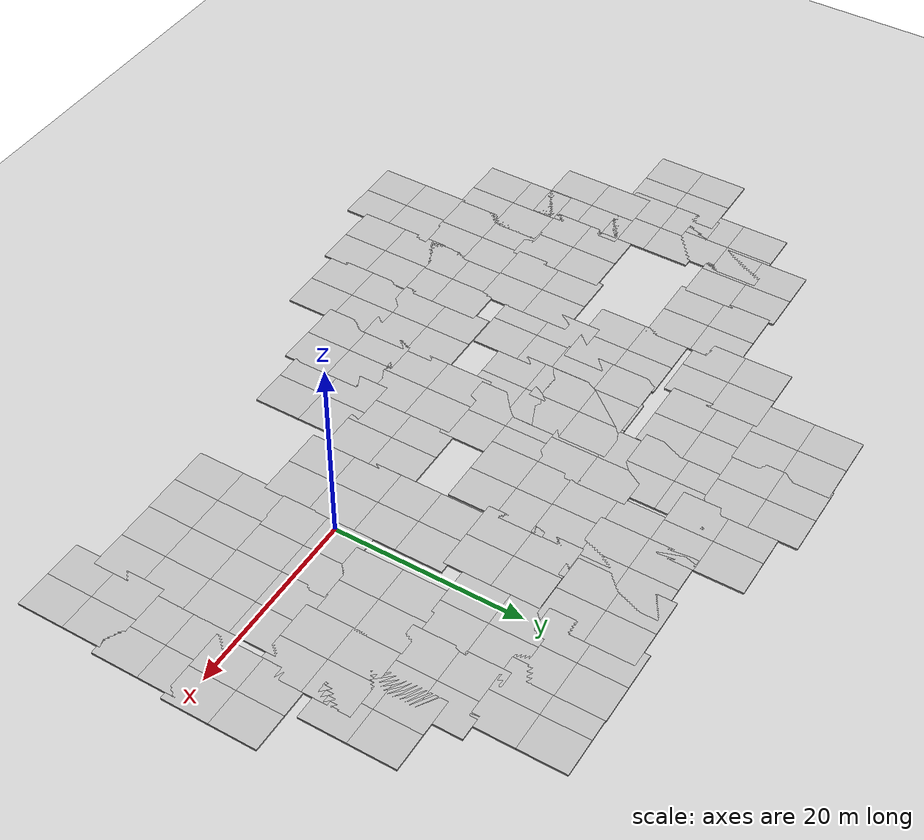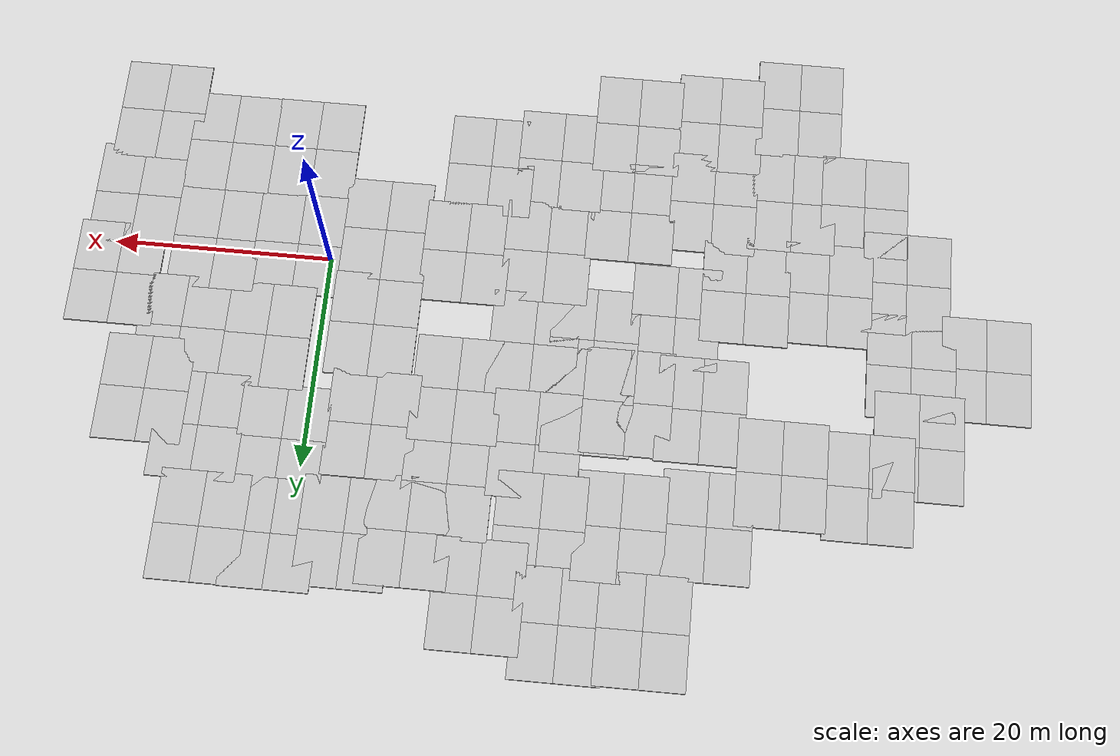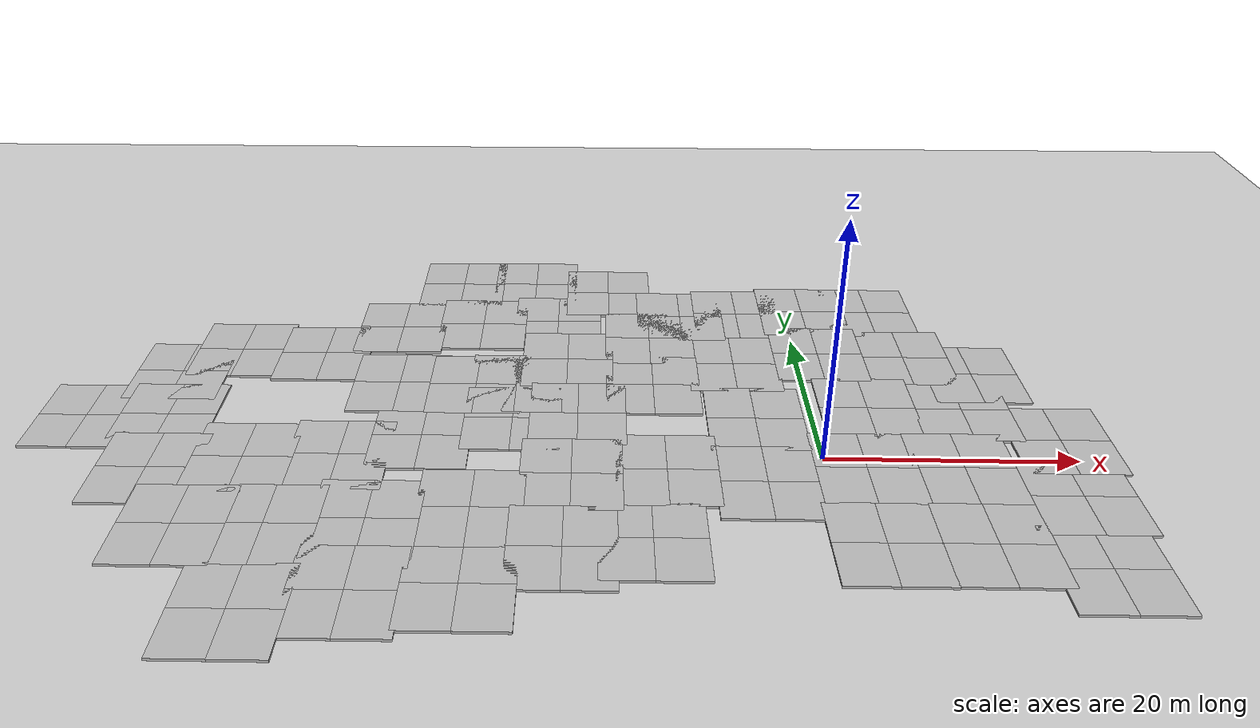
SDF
<sdf version="1.6">
 <world name="default">
  <light name="sun" type="directional">
   <pose>0 0 10 0 -0 0</pose>
   <diffuse>0.8 0.8 0.8 1</diffuse>
   <specular>0.2 0.2 0.2 1</specular>
   <attenuation>
    <range>1000</range>
    <constant>0.9</constant>
    <linear>0.01</linear>
    <quadratic>0.001</quadratic>
   </attenuation>
   <direction>-0.5 0.1 -0.9</direction>
  </light>
  <model name="ground_plane">
   <static>1</static>
   <link name="link">
    <collision name="collision">
     <geometry><plane><normal>0 0 1</normal><size>100 100</size></plane></geometry>
     <surface><friction><ode><mu>100</mu><mu2>50</mu2></ode></friction></surface>
    </collision>
    <visual name="visual">
     <cast_shadows>0</cast_shadows>
     <geometry><plane><normal>0 0 1</normal><size>100 100</size></plane></geometry>
     <material>
      <script><uri>file://media/materials/scripts/gazebo.material</uri><name>Gazebo/Grey</name></script>
     </material>
    </visual>
   </link>
  </model>
  <gravity>0 0 -9.8</gravity>
  <magnetic_field>6e-06 2.3e-05 -4.2e-05</magnetic_field>
  <atmosphere type="adiabatic"/>
  <physics name="default_physics" default="0" type="ode">
   <max_step_size>0.001</max_step_size>
   <real_time_factor>1</real_time_factor>
   <real_time_update_rate>1000</real_time_update_rate>
  </physics>
  <scene><ambient>0.4 0.4 0.4 1</ambient><background>0.7 0.7 0.7 1</background><shadows>1</shadows></scene>
  <spherical_coordinates>
   <surface_model>EARTH_WGS84</surface_model>
   <latitude_deg>0</latitude_deg>
   <longitude_deg>0</longitude_deg>
   <elevation>0</elevation>
   <heading_deg>0</heading_deg>
  </spherical_coordinates>
  <light name="user_point_light_0" type="point">
   <pose>8.28023 -0.456318 1 0 -0 0</pose>
   <diffuse>0.5 0.5 0.5 1</diffuse>
   <specular>0.1 0.1 0.1 1</specular>
   <attenuation>
    <range>20</range>
    <constant>0.5</constant>
    <linear>0.01</linear>
    <quadratic>0.001</quadratic>
   </attenuation>
   <cast_shadows>0</cast_shadows>
   <direction>0 0 -1</direction>
  </light>
  <light name="user_point_light_1" type="point">
   <pose>6.40892 11.96 1 0 -0 0</pose>
   <diffuse>0.5 0.5 0.5 1</diffuse>
   <specular>0.1 0.1 0.1 1</specular>
   <attenuation>
    <range>20</range>
    <constant>0.5</constant>
    <linear>0.01</linear>
    <quadratic>0.001</quadratic>
   </attenuation>
   <cast_shadows>0</cast_shadows>
   <direction>0 0 -1</direction>
  </light>
  <light name="user_point_light_2" type="point">
   <pose>6.12054 -7.71859 1 0 -0 0</pose>
   <diffuse>0.5 0.5 0.5 1</diffuse>
   <specular>0.1 0.1 0.1 1</specular>
   <attenuation>
    <range>20</range>
    <constant>0.5</constant>
    <linear>0.01</linear>
    <quadratic>0.001</quadratic>
   </attenuation>
   <cast_shadows>0</cast_shadows>
   <direction>0 0 -1</direction>
  </light>
  <light name="user_point_light_3" type="point">
   <pose>-8.08161 -3.10917 1 0 -0 0</pose>
   <diffuse>0.5 0.5 0.5 1</diffuse>
   <specular>0.1 0.1 0.1 1</specular>
   <attenuation>
    <range>20</range>
    <constant>0.5</constant>
    <linear>0.01</linear>
    <quadratic>0.001</quadratic>
   </attenuation>
   <cast_shadows>0</cast_shadows>
   <direction>0 0 -1</direction>
  </light>
  <light name="user_point_light_4" type="point">
   <pose>-4.71117 2.539 1 0 -0 0</pose>
   <diffuse>0.5 0.5 0.5 1</diffuse>
   <specular>0.1 0.1 0.1 1</specular>
   <attenuation>
    <range>20</range>
    <constant>0.5</constant>
    <linear>0.01</linear>
    <quadratic>0.001</quadratic>
   </attenuation>
   <cast_shadows>0</cast_shadows>
   <direction>0 0 -1</direction>
  </light>
  <light name="user_point_light_5" type="point">
   <pose>-4.69461 11.7698 1 0 -0 0</pose>
   <diffuse>0.5 0.5 0.5 1</diffuse>
   <specular>0.1 0.1 0.1 1</specular>
   <attenuation>
    <range>20</range>
    <constant>0.5</constant>
    <linear>0.01</linear>
    <quadratic>0.001</quadratic>
   </attenuation>
   <cast_shadows>0</cast_shadows>
   <direction>0 0 -1</direction>
  </light>
  <model name="mud_box">
   <static>1</static>
   <link name="link">
    <collision name="collision"><geometry><box><size>8 10 0.2</size></box></geometry></collision>
    <visual name="visual_1">
     <pose>-2 2.5 0 0 -0 0</pose>
     <cast_shadows>0</cast_shadows>
     <geometry><box><size>4 5 0.2</size></box></geometry>
     <material>
      <script>
       <uri>model://mud_box/materials/scripts</uri>
       <uri>model://mud_box/materials/textures</uri>
       <name>vrc/mud</name>
      </script>
     </material>
    </visual>
    <visual name="visual_2">
     <pose>2 2.5 0 0 -0 0</pose>
     <cast_shadows>0</cast_shadows>
     <geometry><box><size>4 5 0.2</size></box></geometry>
     <material>
      <script>
       <uri>model://mud_box/materials/scripts</uri>
       <uri>model://mud_box/materials/textures</uri>
       <name>vrc/mud</name>
      </script>
     </material>
    </visual>
    <visual name="visual_3">
     <pose>2 -2.5 0 0 -0 0</pose>
     <cast_shadows>0</cast_shadows>
     <geometry><box><size>4 5 0.2</size></box></geometry>
     <material>
      <script>
       <uri>model://mud_box/materials/scripts</uri>
       <uri>model://mud_box/materials/textures</uri>
       <name>vrc/mud</name>
      </script>
     </material>
    </visual>
    <visual name="visual_4">
     <pose>-2 -2.5 0 0 -0 0</pose>
     <cast_shadows>0</cast_shadows>
     <geometry><box><size>4 5 0.2</size></box></geometry>
     <material>
      <script>
       <uri>model://mud_box/materials/scripts</uri>
       <uri>model://mud_box/materials/textures</uri>
       <name>vrc/mud</name>
      </script>
     </material>
    </visual>
   </link>
   <pose>10.8165 -11.0952 0 0 -0 0</pose>
  </model>
  <model name="mud_box_clone">
   <static>1</static>
   <link name="link">
    <collision name="collision"><geometry><box><size>8 10 0.2</size></box></geometry></collision>
    <visual name="visual_1">
     <pose>-2 2.5 0 0 -0 0</pose>
     <cast_shadows>0</cast_shadows>
     <geometry><box><size>4 5 0.2</size></box></geometry>
     <material>
      <script>
       <uri>model://mud_box/materials/scripts</uri>
       <uri>model://mud_box/materials/textures</uri>
       <name>vrc/mud</name>
      </script>
     </material>
    </visual>
    <visual name="visual_2">
     <pose>2 2.5 0 0 -0 0</pose>
     <cast_shadows>0</cast_shadows>
     <geometry><box><size>4 5 0.2</size></box></geometry>
     <material>
      <script>
       <uri>model://mud_box/materials/scripts</uri>
       <uri>model://mud_box/materials/textures</uri>
       <name>vrc/mud</name>
      </script>
     </material>
    </visual>
    <visual name="visual_3">
     <pose>2 -2.5 0 0 -0 0</pose>
     <cast_shadows>0</cast_shadows>
     <geometry><box><size>4 5 0.2</size></box></geometry>
     <material>
      <script>
       <uri>model://mud_box/materials/scripts</uri>
       <uri>model://mud_box/materials/textures</uri>
       <name>vrc/mud</name>
      </script>
     </material>
    </visual>
    <visual name="visual_4">
     <pose>-2 -2.5 0 0 -0 0</pose>
     <cast_shadows>0</cast_shadows>
     <geometry><box><size>4 5 0.2</size></box></geometry>
     <material>
      <script>
       <uri>model://mud_box/materials/scripts</uri>
       <uri>model://mud_box/materials/textures</uri>
       <name>vrc/mud</name>
      </script>
     </material>
    </visual>
   </link>
   <pose>2.87482 -11.1421 0 0 -0 0</pose>
  </model>
  <model name="mud_box_clone_0">
   <static>1</static>
   <link name="link">
    <collision name="collision"><geometry><box><size>8 10 0.2</size></box></geometry></collision>
    <visual name="visual_1">
     <pose>-2 2.5 0 0 -0 0</pose>
     <cast_shadows>0</cast_shadows>
     <geometry><box><size>4 5 0.2</size></box></geometry>
     <material>
      <script>
       <uri>model://mud_box/materials/scripts</uri>
       <uri>model://mud_box/materials/textures</uri>
       <name>vrc/mud</name>
      </script>
     </material>
    </visual>
    <visual name="visual_2">
     <pose>2 2.5 0 0 -0 0</pose>
     <cast_shadows>0</cast_shadows>
     <geometry><box><size>4 5 0.2</size></box></geometry>
     <material>
      <script>
       <uri>model://mud_box/materials/scripts</uri>
       <uri>model://mud_box/materials/textures</uri>
       <name>vrc/mud</name>
      </script>
     </material>
    </visual>
    <visual name="visual_3">
     <pose>2 -2.5 0 0 -0 0</pose>
     <cast_shadows>0</cast_shadows>
     <geometry><box><size>4 5 0.2</size></box></geometry>
     <material>
      <script>
       <uri>model://mud_box/materials/scripts</uri>
       <uri>model://mud_box/materials/textures</uri>
       <name>vrc/mud</name>
      </script>
     </material>
    </visual>
    <visual name="visual_4">
     <pose>-2 -2.5 0 0 -0 0</pose>
     <cast_shadows>0</cast_shadows>
     <geometry><box><size>4 5 0.2</size></box></geometry>
     <material>
      <script>
       <uri>model://mud_box/materials/scripts</uri>
       <uri>model://mud_box/materials/textures</uri>
       <name>vrc/mud</name>
      </script>
     </material>
    </visual>
   </link>
   <pose>10.7714 -1.1411 0 0 -0 0</pose>
  </model>
  <model name="mud_box_clone_1">
   <static>1</static>
   <link name="link">
    <collision name="collision"><geometry><box><size>8 10 0.2</size></box></geometry></collision>
    <visual name="visual_1">
     <pose>-2 2.5 0 0 -0 0</pose>
     <cast_shadows>0</cast_shadows>
     <geometry><box><size>4 5 0.2</size></box></geometry>
     <material>
      <script>
       <uri>model://mud_box/materials/scripts</uri>
       <uri>model://mud_box/materials/textures</uri>
       <name>vrc/mud</name>
      </script>
     </material>
    </visual>
    <visual name="visual_2">
     <pose>2 2.5 0 0 -0 0</pose>
     <cast_shadows>0</cast_shadows>
     <geometry><box><size>4 5 0.2</size></box></geometry>
     <material>
      <script>
       <uri>model://mud_box/materials/scripts</uri>
       <uri>model://mud_box/materials/textures</uri>
       <name>vrc/mud</name>
      </script>
     </material>
    </visual>
    <visual name="visual_3">
     <pose>2 -2.5 0 0 -0 0</pose>
     <cast_shadows>0</cast_shadows>
     <geometry><box><size>4 5 0.2</size></box></geometry>
     <material>
      <script>
       <uri>model://mud_box/materials/scripts</uri>
       <uri>model://mud_box/materials/textures</uri>
       <name>vrc/mud</name>
      </script>
     </material>
    </visual>
    <visual name="visual_4">
     <pose>-2 -2.5 0 0 -0 0</pose>
     <cast_shadows>0</cast_shadows>
     <geometry><box><size>4 5 0.2</size></box></geometry>
     <material>
      <script>
       <uri>model://mud_box/materials/scripts</uri>
       <uri>model://mud_box/materials/textures</uri>
       <name>vrc/mud</name>
      </script>
     </material>
    </visual>
   </link>
   <pose>3.19815 -1.27428 0 0 -0 0</pose>
  </model>
  <model name="mud_box_clone_2">
   <static>1</static>
   <link name="link">
    <collision name="collision"><geometry><box><size>8 10 0.2</size></box></geometry></collision>
    <visual name="visual_1">
     <pose>-2 2.5 0 0 -0 0</pose>
     <cast_shadows>0</cast_shadows>
     <geometry><box><size>4 5 0.2</size></box></geometry>
     <material>
      <script>
       <uri>model://mud_box/materials/scripts</uri>
       <uri>model://mud_box/materials/textures</uri>
       <name>vrc/mud</name>
      </script>
     </material>
    </visual>
    <visual name="visual_2">
     <pose>2 2.5 0 0 -0 0</pose>
     <cast_shadows>0</cast_shadows>
     <geometry><box><size>4 5 0.2</size></box></geometry>
     <material>
      <script>
       <uri>model://mud_box/materials/scripts</uri>
       <uri>model://mud_box/materials/textures</uri>
       <name>vrc/mud</name>
      </script>
     </material>
    </visual>
    <visual name="visual_3">
     <pose>2 -2.5 0 0 -0 0</pose>
     <cast_shadows>0</cast_shadows>
     <geometry><box><size>4 5 0.2</size></box></geometry>
     <material>
      <script>
       <uri>model://mud_box/materials/scripts</uri>
       <uri>model://mud_box/materials/textures</uri>
       <name>vrc/mud</name>
      </script>
     </material>
    </visual>
    <visual name="visual_4">
     <pose>-2 -2.5 0 0 -0 0</pose>
     <cast_shadows>0</cast_shadows>
     <geometry><box><size>4 5 0.2</size></box></geometry>
     <material>
      <script>
       <uri>model://mud_box/materials/scripts</uri>
       <uri>model://mud_box/materials/textures</uri>
       <name>vrc/mud</name>
      </script>
     </material>
    </visual>
   </link>
   <pose>-4.68734 -3.40897 0 0 -0 0</pose>
  </model>
  <model name="mud_box_clone_3">
   <static>1</static>
   <link name="link">
    <collision name="collision"><geometry><box><size>8 10 0.2</size></box></geometry></collision>
    <visual name="visual_1">
     <pose>-2 2.5 0 0 -0 0</pose>
     <cast_shadows>0</cast_shadows>
     <geometry><box><size>4 5 0.2</size></box></geometry>
     <material>
      <script>
       <uri>model://mud_box/materials/scripts</uri>
       <uri>model://mud_box/materials/textures</uri>
       <name>vrc/mud</name>
      </script>
     </material>
    </visual>
    <visual name="visual_2">
     <pose>2 2.5 0 0 -0 0</pose>
     <cast_shadows>0</cast_shadows>
     <geometry><box><size>4 5 0.2</size></box></geometry>
     <material>
      <script>
       <uri>model://mud_box/materials/scripts</uri>
       <uri>model://mud_box/materials/textures</uri>
       <name>vrc/mud</name>
      </script>
     </material>
    </visual>
    <visual name="visual_3">
     <pose>2 -2.5 0 0 -0 0</pose>
     <cast_shadows>0</cast_shadows>
     <geometry><box><size>4 5 0.2</size></box></geometry>
     <material>
      <script>
       <uri>model://mud_box/materials/scripts</uri>
       <uri>model://mud_box/materials/textures</uri>
       <name>vrc/mud</name>
      </script>
     </material>
    </visual>
    <visual name="visual_4">
     <pose>-2 -2.5 0 0 -0 0</pose>
     <cast_shadows>0</cast_shadows>
     <geometry><box><size>4 5 0.2</size></box></geometry>
     <material>
      <script>
       <uri>model://mud_box/materials/scripts</uri>
       <uri>model://mud_box/materials/textures</uri>
       <name>vrc/mud</name>
      </script>
     </material>
    </visual>
   </link>
   <pose>-12.3073 -1.84403 0 0 -0 0</pose>
  </model>
  <model name="mud_box_clone_4">
   <static>1</static>
   <link name="link">
    <collision name="collision"><geometry><box><size>8 10 0.2</size></box></geometry></collision>
    <visual name="visual_1">
     <pose>-2 2.5 0 0 -0 0</pose>
     <cast_shadows>0</cast_shadows>
     <geometry><box><size>4 5 0.2</size></box></geometry>
     <material>
      <script>
       <uri>model://mud_box/materials/scripts</uri>
       <uri>model://mud_box/materials/textures</uri>
       <name>vrc/mud</name>
      </script>
     </material>
    </visual>
    <visual name="visual_2">
     <pose>2 2.5 0 0 -0 0</pose>
     <cast_shadows>0</cast_shadows>
     <geometry><box><size>4 5 0.2</size></box></geometry>
     <material>
      <script>
       <uri>model://mud_box/materials/scripts</uri>
       <uri>model://mud_box/materials/textures</uri>
       <name>vrc/mud</name>
      </script>
     </material>
    </visual>
    <visual name="visual_3">
     <pose>2 -2.5 0 0 -0 0</pose>
     <cast_shadows>0</cast_shadows>
     <geometry><box><size>4 5 0.2</size></box></geometry>
     <material>
      <script>
       <uri>model://mud_box/materials/scripts</uri>
       <uri>model://mud_box/materials/textures</uri>
       <name>vrc/mud</name>
      </script>
     </material>
    </visual>
    <visual name="visual_4">
     <pose>-2 -2.5 0 0 -0 0</pose>
     <cast_shadows>0</cast_shadows>
     <geometry><box><size>4 5 0.2</size></box></geometry>
     <material>
      <script>
       <uri>model://mud_box/materials/scripts</uri>
       <uri>model://mud_box/materials/textures</uri>
       <name>vrc/mud</name>
      </script>
     </material>
    </visual>
   </link>
   <pose>-4.70215 6.03232 0 0 -0 0</pose>
  </model>
  <model name="mud_box_clone_5">
   <static>1</static>
   <link name="link">
    <collision name="collision"><geometry><box><size>8 10 0.2</size></box></geometry></collision>
    <visual name="visual_1">
     <pose>-2 2.5 0 0 -0 0</pose>
     <cast_shadows>0</cast_shadows>
     <geometry><box><size>4 5 0.2</size></box></geometry>
     <material>
      <script>
       <uri>model://mud_box/materials/scripts</uri>
       <uri>model://mud_box/materials/textures</uri>
       <name>vrc/mud</name>
      </script>
     </material>
    </visual>
    <visual name="visual_2">
     <pose>2 2.5 0 0 -0 0</pose>
     <cast_shadows>0</cast_shadows>
     <geometry><box><size>4 5 0.2</size></box></geometry>
     <material>
      <script>
       <uri>model://mud_box/materials/scripts</uri>
       <uri>model://mud_box/materials/textures</uri>
       <name>vrc/mud</name>
      </script>
     </material>
    </visual>
    <visual name="visual_3">
     <pose>2 -2.5 0 0 -0 0</pose>
     <cast_shadows>0</cast_shadows>
     <geometry><box><size>4 5 0.2</size></box></geometry>
     <material>
      <script>
       <uri>model://mud_box/materials/scripts</uri>
       <uri>model://mud_box/materials/textures</uri>
       <name>vrc/mud</name>
      </script>
     </material>
    </visual>
    <visual name="visual_4">
     <pose>-2 -2.5 0 0 -0 0</pose>
     <cast_shadows>0</cast_shadows>
     <geometry><box><size>4 5 0.2</size></box></geometry>
     <material>
      <script>
       <uri>model://mud_box/materials/scripts</uri>
       <uri>model://mud_box/materials/textures</uri>
       <name>vrc/mud</name>
      </script>
     </material>
    </visual>
   </link>
   <pose>4.84706 7.94256 0 0 -0 0</pose>
  </model>
  <model name="mud_box_clone_6">
   <static>1</static>
   <link name="link">
    <collision name="collision"><geometry><box><size>8 10 0.2</size></box></geometry></collision>
    <visual name="visual_1">
     <pose>-2 2.5 0 0 -0 0</pose>
     <cast_shadows>0</cast_shadows>
     <geometry><box><size>4 5 0.2</size></box></geometry>
     <material>
      <script>
       <uri>model://mud_box/materials/scripts</uri>
       <uri>model://mud_box/materials/textures</uri>
       <name>vrc/mud</name>
      </script>
     </material>
    </visual>
    <visual name="visual_2">
     <pose>2 2.5 0 0 -0 0</pose>
     <cast_shadows>0</cast_shadows>
     <geometry><box><size>4 5 0.2</size></box></geometry>
     <material>
      <script>
       <uri>model://mud_box/materials/scripts</uri>
       <uri>model://mud_box/materials/textures</uri>
       <name>vrc/mud</name>
      </script>
     </material>
    </visual>
    <visual name="visual_3">
     <pose>2 -2.5 0 0 -0 0</pose>
     <cast_shadows>0</cast_shadows>
     <geometry><box><size>4 5 0.2</size></box></geometry>
     <material>
      <script>
       <uri>model://mud_box/materials/scripts</uri>
       <uri>model://mud_box/materials/textures</uri>
       <name>vrc/mud</name>
      </script>
     </material>
    </visual>
    <visual name="visual_4">
     <pose>-2 -2.5 0 0 -0 0</pose>
     <cast_shadows>0</cast_shadows>
     <geometry><box><size>4 5 0.2</size></box></geometry>
     <material>
      <script>
       <uri>model://mud_box/materials/scripts</uri>
       <uri>model://mud_box/materials/textures</uri>
       <name>vrc/mud</name>
      </script>
     </material>
    </visual>
   </link>
   <pose>12.6473 7.83678 0 0 -0 0</pose>
  </model>
  <model name="mud_box_clone_7">
   <static>1</static>
   <link name="link">
    <collision name="collision"><geometry><box><size>8 10 0.2</size></box></geometry></collision>
    <visual name="visual_1">
     <pose>-2 2.5 0 0 -0 0</pose>
     <cast_shadows>0</cast_shadows>
     <geometry><box><size>4 5 0.2</size></box></geometry>
     <material>
      <script>
       <uri>model://mud_box/materials/scripts</uri>
       <uri>model://mud_box/materials/textures</uri>
       <name>vrc/mud</name>
      </script>
     </material>
    </visual>
    <visual name="visual_2">
     <pose>2 2.5 0 0 -0 0</pose>
     <cast_shadows>0</cast_shadows>
     <geometry><box><size>4 5 0.2</size></box></geometry>
     <material>
      <script>
       <uri>model://mud_box/materials/scripts</uri>
       <uri>model://mud_box/materials/textures</uri>
       <name>vrc/mud</name>
      </script>
     </material>
    </visual>
    <visual name="visual_3">
     <pose>2 -2.5 0 0 -0 0</pose>
     <cast_shadows>0</cast_shadows>
     <geometry><box><size>4 5 0.2</size></box></geometry>
     <material>
      <script>
       <uri>model://mud_box/materials/scripts</uri>
       <uri>model://mud_box/materials/textures</uri>
       <name>vrc/mud</name>
      </script>
     </material>
    </visual>
    <visual name="visual_4">
     <pose>-2 -2.5 0 0 -0 0</pose>
     <cast_shadows>0</cast_shadows>
     <geometry><box><size>4 5 0.2</size></box></geometry>
     <material>
      <script>
       <uri>model://mud_box/materials/scripts</uri>
       <uri>model://mud_box/materials/textures</uri>
       <name>vrc/mud</name>
      </script>
     </material>
    </visual>
   </link>
   <pose>-5.70582 15.5445 0 0 -0 0</pose>
  </model>
  <model name="mud_box_clone_8">
   <static>1</static>
   <link name="link">
    <collision name="collision"><geometry><box><size>8 10 0.2</size></box></geometry></collision>
    <visual name="visual_1">
     <pose>-2 2.5 0 0 -0 0</pose>
     <cast_shadows>0</cast_shadows>
     <geometry><box><size>4 5 0.2</size></box></geometry>
     <material>
      <script>
       <uri>model://mud_box/materials/scripts</uri>
       <uri>model://mud_box/materials/textures</uri>
       <name>vrc/mud</name>
      </script>
     </material>
    </visual>
    <visual name="visual_2">
     <pose>2 2.5 0 0 -0 0</pose>
     <cast_shadows>0</cast_shadows>
     <geometry><box><size>4 5 0.2</size></box></geometry>
     <material>
      <script>
       <uri>model://mud_box/materials/scripts</uri>
       <uri>model://mud_box/materials/textures</uri>
       <name>vrc/mud</name>
      </script>
     </material>
    </visual>
    <visual name="visual_3">
     <pose>2 -2.5 0 0 -0 0</pose>
     <cast_shadows>0</cast_shadows>
     <geometry><box><size>4 5 0.2</size></box></geometry>
     <material>
      <script>
       <uri>model://mud_box/materials/scripts</uri>
       <uri>model://mud_box/materials/textures</uri>
       <name>vrc/mud</name>
      </script>
     </material>
    </visual>
    <visual name="visual_4">
     <pose>-2 -2.5 0 0 -0 0</pose>
     <cast_shadows>0</cast_shadows>
     <geometry><box><size>4 5 0.2</size></box></geometry>
     <material>
      <script>
       <uri>model://mud_box/materials/scripts</uri>
       <uri>model://mud_box/materials/textures</uri>
       <name>vrc/mud</name>
      </script>
     </material>
    </visual>
   </link>
   <pose>-12.9373 11.5852 0 0 -0 0</pose>
  </model>
  <model name="mud_box_clone_9">
   <static>1</static>
   <link name="link">
    <collision name="collision"><geometry><box><size>8 10 0.2</size></box></geometry></collision>
    <visual name="visual_1">
     <pose>-2 2.5 0 0 -0 0</pose>
     <cast_shadows>0</cast_shadows>
     <geometry><box><size>4 5 0.2</size></box></geometry>
     <material>
      <script>
       <uri>model://mud_box/materials/scripts</uri>
       <uri>model://mud_box/materials/textures</uri>
       <name>vrc/mud</name>
      </script>
     </material>
    </visual>
    <visual name="visual_2">
     <pose>2 2.5 0 0 -0 0</pose>
     <cast_shadows>0</cast_shadows>
     <geometry><box><size>4 5 0.2</size></box></geometry>
     <material>
      <script>
       <uri>model://mud_box/materials/scripts</uri>
       <uri>model://mud_box/materials/textures</uri>
       <name>vrc/mud</name>
      </script>
     </material>
    </visual>
    <visual name="visual_3">
     <pose>2 -2.5 0 0 -0 0</pose>
     <cast_shadows>0</cast_shadows>
     <geometry><box><size>4 5 0.2</size></box></geometry>
     <material>
      <script>
       <uri>model://mud_box/materials/scripts</uri>
       <uri>model://mud_box/materials/textures</uri>
       <name>vrc/mud</name>
      </script>
     </material>
    </visual>
    <visual name="visual_4">
     <pose>-2 -2.5 0 0 -0 0</pose>
     <cast_shadows>0</cast_shadows>
     <geometry><box><size>4 5 0.2</size></box></geometry>
     <material>
      <script>
       <uri>model://mud_box/materials/scripts</uri>
       <uri>model://mud_box/materials/textures</uri>
       <name>vrc/mud</name>
      </script>
     </material>
    </visual>
   </link>
   <pose>2.05999 17.5856 0 0 -0 0</pose>
  </model>
  <model name="mud_box_clone_10">
   <static>1</static>
   <link name="link">
    <collision name="collision"><geometry><box><size>8 10 0.2</size></box></geometry></collision>
    <visual name="visual_1">
     <pose>-2 2.5 0 0 -0 0</pose>
     <cast_shadows>0</cast_shadows>
     <geometry><box><size>4 5 0.2</size></box></geometry>
     <material>
      <script>
       <uri>model://mud_box/materials/scripts</uri>
       <uri>model://mud_box/materials/textures</uri>
       <name>vrc/mud</name>
      </script>
     </material>
    </visual>
    <visual name="visual_2">
     <pose>2 2.5 0 0 -0 0</pose>
     <cast_shadows>0</cast_shadows>
     <geometry><box><size>4 5 0.2</size></box></geometry>
     <material>
      <script>
       <uri>model://mud_box/materials/scripts</uri>
       <uri>model://mud_box/materials/textures</uri>
       <name>vrc/mud</name>
      </script>
     </material>
    </visual>
    <visual name="visual_3">
     <pose>2 -2.5 0 0 -0 0</pose>
     <cast_shadows>0</cast_shadows>
     <geometry><box><size>4 5 0.2</size></box></geometry>
     <material>
      <script>
       <uri>model://mud_box/materials/scripts</uri>
       <uri>model://mud_box/materials/textures</uri>
       <name>vrc/mud</name>
      </script>
     </material>
    </visual>
    <visual name="visual_4">
     <pose>-2 -2.5 0 0 -0 0</pose>
     <cast_shadows>0</cast_shadows>
     <geometry><box><size>4 5 0.2</size></box></geometry>
     <material>
      <script>
       <uri>model://mud_box/materials/scripts</uri>
       <uri>model://mud_box/materials/textures</uri>
       <name>vrc/mud</name>
      </script>
     </material>
    </visual>
   </link>
   <pose>9.61548 17.0189 0 0 -0 0</pose>
  </model>
  <model name="mud_box_clone_8_clone">
   <static>1</static>
   <link name="link">
    <collision name="collision"><geometry><box><size>8 10 0.2</size></box></geometry></collision>
    <visual name="visual_1">
     <pose>-2 2.5 0 0 -0 0</pose>
     <cast_shadows>0</cast_shadows>
     <geometry><box><size>4 5 0.2</size></box></geometry>
     <material>
      <script>
       <uri>model://mud_box/materials/scripts</uri>
       <uri>model://mud_box/materials/textures</uri>
       <name>vrc/mud</name>
      </script>
     </material>
    </visual>
    <visual name="visual_2">
     <pose>2 2.5 0 0 -0 0</pose>
     <cast_shadows>0</cast_shadows>
     <geometry><box><size>4 5 0.2</size></box></geometry>
     <material>
      <script>
       <uri>model://mud_box/materials/scripts</uri>
       <uri>model://mud_box/materials/textures</uri>
       <name>vrc/mud</name>
      </script>
     </material>
    </visual>
    <visual name="visual_3">
     <pose>2 -2.5 0 0 -0 0</pose>
     <cast_shadows>0</cast_shadows>
     <geometry><box><size>4 5 0.2</size></box></geometry>
     <material>
      <script>
       <uri>model://mud_box/materials/scripts</uri>
       <uri>model://mud_box/materials/textures</uri>
       <name>vrc/mud</name>
      </script>
     </material>
    </visual>
    <visual name="visual_4">
     <pose>-2 -2.5 0 0 -0 0</pose>
     <cast_shadows>0</cast_shadows>
     <geometry><box><size>4 5 0.2</size></box></geometry>
     <material>
      <script>
       <uri>model://mud_box/materials/scripts</uri>
       <uri>model://mud_box/materials/textures</uri>
       <name>vrc/mud</name>
      </script>
     </material>
    </visual>
   </link>
   <pose>-12.9975 20.4027 0 0 -0 0</pose>
  </model>
  <model name="mud_box_clone_8_clone_0">
   <static>1</static>
   <link name="link">
    <collision name="collision"><geometry><box><size>8 10 0.2</size></box></geometry></collision>
    <visual name="visual_1">
     <pose>-2 2.5 0 0 -0 0</pose>
     <cast_shadows>0</cast_shadows>
     <geometry><box><size>4 5 0.2</size></box></geometry>
     <material>
      <script>
       <uri>model://mud_box/materials/scripts</uri>
       <uri>model://mud_box/materials/textures</uri>
       <name>vrc/mud</name>
      </script>
     </material>
    </visual>
    <visual name="visual_2">
     <pose>2 2.5 0 0 -0 0</pose>
     <cast_shadows>0</cast_shadows>
     <geometry><box><size>4 5 0.2</size></box></geometry>
     <material>
      <script>
       <uri>model://mud_box/materials/scripts</uri>
       <uri>model://mud_box/materials/textures</uri>
       <name>vrc/mud</name>
      </script>
     </material>
    </visual>
    <visual name="visual_3">
     <pose>2 -2.5 0 0 -0 0</pose>
     <cast_shadows>0</cast_shadows>
     <geometry><box><size>4 5 0.2</size></box></geometry>
     <material>
      <script>
       <uri>model://mud_box/materials/scripts</uri>
       <uri>model://mud_box/materials/textures</uri>
       <name>vrc/mud</name>
      </script>
     </material>
    </visual>
    <visual name="visual_4">
     <pose>-2 -2.5 0 0 -0 0</pose>
     <cast_shadows>0</cast_shadows>
     <geometry><box><size>4 5 0.2</size></box></geometry>
     <material>
      <script>
       <uri>model://mud_box/materials/scripts</uri>
       <uri>model://mud_box/materials/textures</uri>
       <name>vrc/mud</name>
      </script>
     </material>
    </visual>
   </link>
   <pose>-4.56717 25.6056 0 0 -0 0</pose>
  </model>
  <model name="mud_box_clone_8_clone_1">
   <static>1</static>
   <link name="link">
    <collision name="collision"><geometry><box><size>8 10 0.2</size></box></geometry></collision>
    <visual name="visual_1">
     <pose>-2 2.5 0 0 -0 0</pose>
     <cast_shadows>0</cast_shadows>
     <geometry><box><size>4 5 0.2</size></box></geometry>
     <material>
      <script>
       <uri>model://mud_box/materials/scripts</uri>
       <uri>model://mud_box/materials/textures</uri>
       <name>vrc/mud</name>
      </script>
     </material>
    </visual>
    <visual name="visual_2">
     <pose>2 2.5 0 0 -0 0</pose>
     <cast_shadows>0</cast_shadows>
     <geometry><box><size>4 5 0.2</size></box></geometry>
     <material>
      <script>
       <uri>model://mud_box/materials/scripts</uri>
       <uri>model://mud_box/materials/textures</uri>
       <name>vrc/mud</name>
      </script>
     </material>
    </visual>
    <visual name="visual_3">
     <pose>2 -2.5 0 0 -0 0</pose>
     <cast_shadows>0</cast_shadows>
     <geometry><box><size>4 5 0.2</size></box></geometry>
     <material>
      <script>
       <uri>model://mud_box/materials/scripts</uri>
       <uri>model://mud_box/materials/textures</uri>
       <name>vrc/mud</name>
      </script>
     </material>
    </visual>
    <visual name="visual_4">
     <pose>-2 -2.5 0 0 -0 0</pose>
     <cast_shadows>0</cast_shadows>
     <geometry><box><size>4 5 0.2</size></box></geometry>
     <material>
      <script>
       <uri>model://mud_box/materials/scripts</uri>
       <uri>model://mud_box/materials/textures</uri>
       <name>vrc/mud</name>
      </script>
     </material>
    </visual>
   </link>
   <pose>8.06738 26.1887 0 0 -0 0</pose>
  </model>
  <model name="mud_box_clone_8_clone_2">
   <static>1</static>
   <link name="link">
    <collision name="collision"><geometry><box><size>8 10 0.2</size></box></geometry></collision>
    <visual name="visual_1">
     <pose>-2 2.5 0 0 -0 0</pose>
     <cast_shadows>0</cast_shadows>
     <geometry><box><size>4 5 0.2</size></box></geometry>
     <material>
      <script>
       <uri>model://mud_box/materials/scripts</uri>
       <uri>model://mud_box/materials/textures</uri>
       <name>vrc/mud</name>
      </script>
     </material>
    </visual>
    <visual name="visual_2">
     <pose>2 2.5 0 0 -0 0</pose>
     <cast_shadows>0</cast_shadows>
     <geometry><box><size>4 5 0.2</size></box></geometry>
     <material>
      <script>
       <uri>model://mud_box/materials/scripts</uri>
       <uri>model://mud_box/materials/textures</uri>
       <name>vrc/mud</name>
      </script>
     </material>
    </visual>
    <visual name="visual_3">
     <pose>2 -2.5 0 0 -0 0</pose>
     <cast_shadows>0</cast_shadows>
     <geometry><box><size>4 5 0.2</size></box></geometry>
     <material>
      <script>
       <uri>model://mud_box/materials/scripts</uri>
       <uri>model://mud_box/materials/textures</uri>
       <name>vrc/mud</name>
      </script>
     </material>
    </visual>
    <visual name="visual_4">
     <pose>-2 -2.5 0 0 -0 0</pose>
     <cast_shadows>0</cast_shadows>
     <geometry><box><size>4 5 0.2</size></box></geometry>
     <material>
      <script>
       <uri>model://mud_box/materials/scripts</uri>
       <uri>model://mud_box/materials/textures</uri>
       <name>vrc/mud</name>
      </script>
     </material>
    </visual>
   </link>
   <pose>-9.95414 25.0042 0 0 -0 0</pose>
  </model>
  <model name="mud_box_clone_8_clone_3">
   <static>1</static>
   <link name="link">
    <collision name="collision"><geometry><box><size>8 10 0.2</size></box></geometry></collision>
    <visual name="visual_1">
     <pose>-2 2.5 0 0 -0 0</pose>
     <cast_shadows>0</cast_shadows>
     <geometry><box><size>4 5 0.2</size></box></geometry>
     <material>
      <script>
       <uri>model://mud_box/materials/scripts</uri>
       <uri>model://mud_box/materials/textures</uri>
       <name>vrc/mud</name>
      </script>
     </material>
    </visual>
    <visual name="visual_2">
     <pose>2 2.5 0 0 -0 0</pose>
     <cast_shadows>0</cast_shadows>
     <geometry><box><size>4 5 0.2</size></box></geometry>
     <material>
      <script>
       <uri>model://mud_box/materials/scripts</uri>
       <uri>model://mud_box/materials/textures</uri>
       <name>vrc/mud</name>
      </script>
     </material>
    </visual>
    <visual name="visual_3">
     <pose>2 -2.5 0 0 -0 0</pose>
     <cast_shadows>0</cast_shadows>
     <geometry><box><size>4 5 0.2</size></box></geometry>
     <material>
      <script>
       <uri>model://mud_box/materials/scripts</uri>
       <uri>model://mud_box/materials/textures</uri>
       <name>vrc/mud</name>
      </script>
     </material>
    </visual>
    <visual name="visual_4">
     <pose>-2 -2.5 0 0 -0 0</pose>
     <cast_shadows>0</cast_shadows>
     <geometry><box><size>4 5 0.2</size></box></geometry>
     <material>
      <script>
       <uri>model://mud_box/materials/scripts</uri>
       <uri>model://mud_box/materials/textures</uri>
       <name>vrc/mud</name>
      </script>
     </material>
    </visual>
   </link>
   <pose>1.75909 26.2514 0 0 -0 0</pose>
  </model>
  <model name="mud_box_clone_8_clone_4">
   <static>1</static>
   <link name="link">
    <collision name="collision"><geometry><box><size>8 10 0.2</size></box></geometry></collision>
    <visual name="visual_1">
     <pose>-2 2.5 0 0 -0 0</pose>
     <cast_shadows>0</cast_shadows>
     <geometry><box><size>4 5 0.2</size></box></geometry>
     <material>
      <script>
       <uri>model://mud_box/materials/scripts</uri>
       <uri>model://mud_box/materials/textures</uri>
       <name>vrc/mud</name>
      </script>
     </material>
    </visual>
    <visual name="visual_2">
     <pose>2 2.5 0 0 -0 0</pose>
     <cast_shadows>0</cast_shadows>
     <geometry><box><size>4 5 0.2</size></box></geometry>
     <material>
      <script>
       <uri>model://mud_box/materials/scripts</uri>
       <uri>model://mud_box/materials/textures</uri>
       <name>vrc/mud</name>
      </script>
     </material>
    </visual>
    <visual name="visual_3">
     <pose>2 -2.5 0 0 -0 0</pose>
     <cast_shadows>0</cast_shadows>
     <geometry><box><size>4 5 0.2</size></box></geometry>
     <material>
      <script>
       <uri>model://mud_box/materials/scripts</uri>
       <uri>model://mud_box/materials/textures</uri>
       <name>vrc/mud</name>
      </script>
     </material>
    </visual>
    <visual name="visual_4">
     <pose>-2 -2.5 0 0 -0 0</pose>
     <cast_shadows>0</cast_shadows>
     <geometry><box><size>4 5 0.2</size></box></geometry>
     <material>
      <script>
       <uri>model://mud_box/materials/scripts</uri>
       <uri>model://mud_box/materials/textures</uri>
       <name>vrc/mud</name>
      </script>
     </material>
    </visual>
   </link>
   <pose>14.966 14.0075 0 0 -0 0</pose>
  </model>
  <model name="mud_box_clone_8_clone_5">
   <static>1</static>
   <link name="link">
    <collision name="collision"><geometry><box><size>8 10 0.2</size></box></geometry></collision>
    <visual name="visual_1">
     <pose>-2 2.5 0 0 -0 0</pose>
     <cast_shadows>0</cast_shadows>
     <geometry><box><size>4 5 0.2</size></box></geometry>
     <material>
      <script>
       <uri>model://mud_box/materials/scripts</uri>
       <uri>model://mud_box/materials/textures</uri>
       <name>vrc/mud</name>
      </script>
     </material>
    </visual>
    <visual name="visual_2">
     <pose>2 2.5 0 0 -0 0</pose>
     <cast_shadows>0</cast_shadows>
     <geometry><box><size>4 5 0.2</size></box></geometry>
     <material>
      <script>
       <uri>model://mud_box/materials/scripts</uri>
       <uri>model://mud_box/materials/textures</uri>
       <name>vrc/mud</name>
      </script>
     </material>
    </visual>
    <visual name="visual_3">
     <pose>2 -2.5 0 0 -0 0</pose>
     <cast_shadows>0</cast_shadows>
     <geometry><box><size>4 5 0.2</size></box></geometry>
     <material>
      <script>
       <uri>model://mud_box/materials/scripts</uri>
       <uri>model://mud_box/materials/textures</uri>
       <name>vrc/mud</name>
      </script>
     </material>
    </visual>
    <visual name="visual_4">
     <pose>-2 -2.5 0 0 -0 0</pose>
     <cast_shadows>0</cast_shadows>
     <geometry><box><size>4 5 0.2</size></box></geometry>
     <material>
      <script>
       <uri>model://mud_box/materials/scripts</uri>
       <uri>model://mud_box/materials/textures</uri>
       <name>vrc/mud</name>
      </script>
     </material>
    </visual>
   </link>
   <pose>19.4294 3.07828 0 0 -0 0</pose>
  </model>
  <model name="mud_box_clone_8_clone_6">
   <static>1</static>
   <link name="link">
    <collision name="collision"><geometry><box><size>8 10 0.2</size></box></geometry></collision>
    <visual name="visual_1">
     <pose>-2 2.5 0 0 -0 0</pose>
     <cast_shadows>0</cast_shadows>
     <geometry><box><size>4 5 0.2</size></box></geometry>
     <material>
      <script>
       <uri>model://mud_box/materials/scripts</uri>
       <uri>model://mud_box/materials/textures</uri>
       <name>vrc/mud</name>
      </script>
     </material>
    </visual>
    <visual name="visual_2">
     <pose>2 2.5 0 0 -0 0</pose>
     <cast_shadows>0</cast_shadows>
     <geometry><box><size>4 5 0.2</size></box></geometry>
     <material>
      <script>
       <uri>model://mud_box/materials/scripts</uri>
       <uri>model://mud_box/materials/textures</uri>
       <name>vrc/mud</name>
      </script>
     </material>
    </visual>
    <visual name="visual_3">
     <pose>2 -2.5 0 0 -0 0</pose>
     <cast_shadows>0</cast_shadows>
     <geometry><box><size>4 5 0.2</size></box></geometry>
     <material>
      <script>
       <uri>model://mud_box/materials/scripts</uri>
       <uri>model://mud_box/materials/textures</uri>
       <name>vrc/mud</name>
      </script>
     </material>
    </visual>
    <visual name="visual_4">
     <pose>-2 -2.5 0 0 -0 0</pose>
     <cast_shadows>0</cast_shadows>
     <geometry><box><size>4 5 0.2</size></box></geometry>
     <material>
      <script>
       <uri>model://mud_box/materials/scripts</uri>
       <uri>model://mud_box/materials/textures</uri>
       <name>vrc/mud</name>
      </script>
     </material>
    </visual>
   </link>
   <pose>18.7481 -4.92195 0 0 -0 0</pose>
  </model>
  <model name="mud_box_clone_8_clone_7">
   <static>1</static>
   <link name="link">
    <collision name="collision"><geometry><box><size>8 10 0.2</size></box></geometry></collision>
    <visual name="visual_1">
     <pose>-2 2.5 0 0 -0 0</pose>
     <cast_shadows>0</cast_shadows>
     <geometry><box><size>4 5 0.2</size></box></geometry>
     <material>
      <script>
       <uri>model://mud_box/materials/scripts</uri>
       <uri>model://mud_box/materials/textures</uri>
       <name>vrc/mud</name>
      </script>
     </material>
    </visual>
    <visual name="visual_2">
     <pose>2 2.5 0 0 -0 0</pose>
     <cast_shadows>0</cast_shadows>
     <geometry><box><size>4 5 0.2</size></box></geometry>
     <material>
      <script>
       <uri>model://mud_box/materials/scripts</uri>
       <uri>model://mud_box/materials/textures</uri>
       <name>vrc/mud</name>
      </script>
     </material>
    </visual>
    <visual name="visual_3">
     <pose>2 -2.5 0 0 -0 0</pose>
     <cast_shadows>0</cast_shadows>
     <geometry><box><size>4 5 0.2</size></box></geometry>
     <material>
      <script>
       <uri>model://mud_box/materials/scripts</uri>
       <uri>model://mud_box/materials/textures</uri>
       <name>vrc/mud</name>
      </script>
     </material>
    </visual>
    <visual name="visual_4">
     <pose>-2 -2.5 0 0 -0 0</pose>
     <cast_shadows>0</cast_shadows>
     <geometry><box><size>4 5 0.2</size></box></geometry>
     <material>
      <script>
       <uri>model://mud_box/materials/scripts</uri>
       <uri>model://mud_box/materials/textures</uri>
       <name>vrc/mud</name>
      </script>
     </material>
    </visual>
   </link>
   <pose>17.9123 -13.8418 0 0 -0 0</pose>
  </model>
  <model name="mud_box_clone_8_clone_8">
   <static>1</static>
   <link name="link">
    <collision name="collision"><geometry><box><size>8 10 0.2</size></box></geometry></collision>
    <visual name="visual_1">
     <pose>-2 2.5 0 0 -0 0</pose>
     <cast_shadows>0</cast_shadows>
     <geometry><box><size>4 5 0.2</size></box></geometry>
     <material>
      <script>
       <uri>model://mud_box/materials/scripts</uri>
       <uri>model://mud_box/materials/textures</uri>
       <name>vrc/mud</name>
      </script>
     </material>
    </visual>
    <visual name="visual_2">
     <pose>2 2.5 0 0 -0 0</pose>
     <cast_shadows>0</cast_shadows>
     <geometry><box><size>4 5 0.2</size></box></geometry>
     <material>
      <script>
       <uri>model://mud_box/materials/scripts</uri>
       <uri>model://mud_box/materials/textures</uri>
       <name>vrc/mud</name>
      </script>
     </material>
    </visual>
    <visual name="visual_3">
     <pose>2 -2.5 0 0 -0 0</pose>
     <cast_shadows>0</cast_shadows>
     <geometry><box><size>4 5 0.2</size></box></geometry>
     <material>
      <script>
       <uri>model://mud_box/materials/scripts</uri>
       <uri>model://mud_box/materials/textures</uri>
       <name>vrc/mud</name>
      </script>
     </material>
    </visual>
    <visual name="visual_4">
     <pose>-2 -2.5 0 0 -0 0</pose>
     <cast_shadows>0</cast_shadows>
     <geometry><box><size>4 5 0.2</size></box></geometry>
     <material>
      <script>
       <uri>model://mud_box/materials/scripts</uri>
       <uri>model://mud_box/materials/textures</uri>
       <name>vrc/mud</name>
      </script>
     </material>
    </visual>
   </link>
   <pose>-13.6916 -10.8668 0 0 -0 0</pose>
  </model>
  <model name="mud_box_clone_8_clone_9">
   <static>1</static>
   <link name="link">
    <collision name="collision"><geometry><box><size>8 10 0.2</size></box></geometry></collision>
    <visual name="visual_1">
     <pose>-2 2.5 0 0 -0 0</pose>
     <cast_shadows>0</cast_shadows>
     <geometry><box><size>4 5 0.2</size></box></geometry>
     <material>
      <script>
       <uri>model://mud_box/materials/scripts</uri>
       <uri>model://mud_box/materials/textures</uri>
       <name>vrc/mud</name>
      </script>
     </material>
    </visual>
    <visual name="visual_2">
     <pose>2 2.5 0 0 -0 0</pose>
     <cast_shadows>0</cast_shadows>
     <geometry><box><size>4 5 0.2</size></box></geometry>
     <material>
      <script>
       <uri>model://mud_box/materials/scripts</uri>
       <uri>model://mud_box/materials/textures</uri>
       <name>vrc/mud</name>
      </script>
     </material>
    </visual>
    <visual name="visual_3">
     <pose>2 -2.5 0 0 -0 0</pose>
     <cast_shadows>0</cast_shadows>
     <geometry><box><size>4 5 0.2</size></box></geometry>
     <material>
      <script>
       <uri>model://mud_box/materials/scripts</uri>
       <uri>model://mud_box/materials/textures</uri>
       <name>vrc/mud</name>
      </script>
     </material>
    </visual>
    <visual name="visual_4">
     <pose>-2 -2.5 0 0 -0 0</pose>
     <cast_shadows>0</cast_shadows>
     <geometry><box><size>4 5 0.2</size></box></geometry>
     <material>
      <script>
       <uri>model://mud_box/materials/scripts</uri>
       <uri>model://mud_box/materials/textures</uri>
       <name>vrc/mud</name>
      </script>
     </material>
    </visual>
   </link>
   <pose>-20.2139 -12.0212 0 0 -0 0</pose>
  </model>
  <model name="mud_box_clone_8_clone_10">
   <static>1</static>
   <link name="link">
    <collision name="collision"><geometry><box><size>8 10 0.2</size></box></geometry></collision>
    <visual name="visual_1">
     <pose>-2 2.5 0 0 -0 0</pose>
     <cast_shadows>0</cast_shadows>
     <geometry><box><size>4 5 0.2</size></box></geometry>
     <material>
      <script>
       <uri>model://mud_box/materials/scripts</uri>
       <uri>model://mud_box/materials/textures</uri>
       <name>vrc/mud</name>
      </script>
     </material>
    </visual>
    <visual name="visual_2">
     <pose>2 2.5 0 0 -0 0</pose>
     <cast_shadows>0</cast_shadows>
     <geometry><box><size>4 5 0.2</size></box></geometry>
     <material>
      <script>
       <uri>model://mud_box/materials/scripts</uri>
       <uri>model://mud_box/materials/textures</uri>
       <name>vrc/mud</name>
      </script>
     </material>
    </visual>
    <visual name="visual_3">
     <pose>2 -2.5 0 0 -0 0</pose>
     <cast_shadows>0</cast_shadows>
     <geometry><box><size>4 5 0.2</size></box></geometry>
     <material>
      <script>
       <uri>model://mud_box/materials/scripts</uri>
       <uri>model://mud_box/materials/textures</uri>
       <name>vrc/mud</name>
      </script>
     </material>
    </visual>
    <visual name="visual_4">
     <pose>-2 -2.5 0 0 -0 0</pose>
     <cast_shadows>0</cast_shadows>
     <geometry><box><size>4 5 0.2</size></box></geometry>
     <material>
      <script>
       <uri>model://mud_box/materials/scripts</uri>
       <uri>model://mud_box/materials/textures</uri>
       <name>vrc/mud</name>
      </script>
     </material>
    </visual>
   </link>
   <pose>-19.7384 -2.56167 0 0 -0 0</pose>
  </model>
  <model name="mud_box_clone_8_clone_11">
   <static>1</static>
   <link name="link">
    <collision name="collision"><geometry><box><size>8 10 0.2</size></box></geometry></collision>
    <visual name="visual_1">
     <pose>-2 2.5 0 0 -0 0</pose>
     <cast_shadows>0</cast_shadows>
     <geometry><box><size>4 5 0.2</size></box></geometry>
     <material>
      <script>
       <uri>model://mud_box/materials/scripts</uri>
       <uri>model://mud_box/materials/textures</uri>
       <name>vrc/mud</name>
      </script>
     </material>
    </visual>
    <visual name="visual_2">
     <pose>2 2.5 0 0 -0 0</pose>
     <cast_shadows>0</cast_shadows>
     <geometry><box><size>4 5 0.2</size></box></geometry>
     <material>
      <script>
       <uri>model://mud_box/materials/scripts</uri>
       <uri>model://mud_box/materials/textures</uri>
       <name>vrc/mud</name>
      </script>
     </material>
    </visual>
    <visual name="visual_3">
     <pose>2 -2.5 0 0 -0 0</pose>
     <cast_shadows>0</cast_shadows>
     <geometry><box><size>4 5 0.2</size></box></geometry>
     <material>
      <script>
       <uri>model://mud_box/materials/scripts</uri>
       <uri>model://mud_box/materials/textures</uri>
       <name>vrc/mud</name>
      </script>
     </material>
    </visual>
    <visual name="visual_4">
     <pose>-2 -2.5 0 0 -0 0</pose>
     <cast_shadows>0</cast_shadows>
     <geometry><box><size>4 5 0.2</size></box></geometry>
     <material>
      <script>
       <uri>model://mud_box/materials/scripts</uri>
       <uri>model://mud_box/materials/textures</uri>
       <name>vrc/mud</name>
      </script>
     </material>
    </visual>
   </link>
   <pose>-19.3537 6.59933 0 0 -0 0</pose>
  </model>
  <model name="mud_box_clone_8_clone_12">
   <static>1</static>
   <link name="link">
    <collision name="collision"><geometry><box><size>8 10 0.2</size></box></geometry></collision>
    <visual name="visual_1">
     <pose>-2 2.5 0 0 -0 0</pose>
     <cast_shadows>0</cast_shadows>
     <geometry><box><size>4 5 0.2</size></box></geometry>
     <material>
      <script>
       <uri>model://mud_box/materials/scripts</uri>
       <uri>model://mud_box/materials/textures</uri>
       <name>vrc/mud</name>
      </script>
     </material>
    </visual>
    <visual name="visual_2">
     <pose>2 2.5 0 0 -0 0</pose>
     <cast_shadows>0</cast_shadows>
     <geometry><box><size>4 5 0.2</size></box></geometry>
     <material>
      <script>
       <uri>model://mud_box/materials/scripts</uri>
       <uri>model://mud_box/materials/textures</uri>
       <name>vrc/mud</name>
      </script>
     </material>
    </visual>
    <visual name="visual_3">
     <pose>2 -2.5 0 0 -0 0</pose>
     <cast_shadows>0</cast_shadows>
     <geometry><box><size>4 5 0.2</size></box></geometry>
     <material>
      <script>
       <uri>model://mud_box/materials/scripts</uri>
       <uri>model://mud_box/materials/textures</uri>
       <name>vrc/mud</name>
      </script>
     </material>
    </visual>
    <visual name="visual_4">
     <pose>-2 -2.5 0 0 -0 0</pose>
     <cast_shadows>0</cast_shadows>
     <geometry><box><size>4 5 0.2</size></box></geometry>
     <material>
      <script>
       <uri>model://mud_box/materials/scripts</uri>
       <uri>model://mud_box/materials/textures</uri>
       <name>vrc/mud</name>
      </script>
     </material>
    </visual>
   </link>
   <pose>-20.3945 16.0961 0 0 -0 0</pose>
  </model>
  <model name="mud_box_clone_8_clone_13">
   <static>1</static>
   <link name="link">
    <collision name="collision"><geometry><box><size>8 10 0.2</size></box></geometry></collision>
    <visual name="visual_1">
     <pose>-2 2.5 0 0 -0 0</pose>
     <cast_shadows>0</cast_shadows>
     <geometry><box><size>4 5 0.2</size></box></geometry>
     <material>
      <script>
       <uri>model://mud_box/materials/scripts</uri>
       <uri>model://mud_box/materials/textures</uri>
       <name>vrc/mud</name>
      </script>
     </material>
    </visual>
    <visual name="visual_2">
     <pose>2 2.5 0 0 -0 0</pose>
     <cast_shadows>0</cast_shadows>
     <geometry><box><size>4 5 0.2</size></box></geometry>
     <material>
      <script>
       <uri>model://mud_box/materials/scripts</uri>
       <uri>model://mud_box/materials/textures</uri>
       <name>vrc/mud</name>
      </script>
     </material>
    </visual>
    <visual name="visual_3">
     <pose>2 -2.5 0 0 -0 0</pose>
     <cast_shadows>0</cast_shadows>
     <geometry><box><size>4 5 0.2</size></box></geometry>
     <material>
      <script>
       <uri>model://mud_box/materials/scripts</uri>
       <uri>model://mud_box/materials/textures</uri>
       <name>vrc/mud</name>
      </script>
     </material>
    </visual>
    <visual name="visual_4">
     <pose>-2 -2.5 0 0 -0 0</pose>
     <cast_shadows>0</cast_shadows>
     <geometry><box><size>4 5 0.2</size></box></geometry>
     <material>
      <script>
       <uri>model://mud_box/materials/scripts</uri>
       <uri>model://mud_box/materials/textures</uri>
       <name>vrc/mud</name>
      </script>
     </material>
    </visual>
   </link>
   <pose>-16.6864 30.0793 0 0 -0 0</pose>
  </model>
  <model name="mud_box_clone_8_clone_14">
   <static>1</static>
   <link name="link">
    <collision name="collision"><geometry><box><size>8 10 0.2</size></box></geometry></collision>
    <visual name="visual_1">
     <pose>-2 2.5 0 0 -0 0</pose>
     <cast_shadows>0</cast_shadows>
     <geometry><box><size>4 5 0.2</size></box></geometry>
     <material>
      <script>
       <uri>model://mud_box/materials/scripts</uri>
       <uri>model://mud_box/materials/textures</uri>
       <name>vrc/mud</name>
      </script>
     </material>
    </visual>
    <visual name="visual_2">
     <pose>2 2.5 0 0 -0 0</pose>
     <cast_shadows>0</cast_shadows>
     <geometry><box><size>4 5 0.2</size></box></geometry>
     <material>
      <script>
       <uri>model://mud_box/materials/scripts</uri>
       <uri>model://mud_box/materials/textures</uri>
       <name>vrc/mud</name>
      </script>
     </material>
    </visual>
    <visual name="visual_3">
     <pose>2 -2.5 0 0 -0 0</pose>
     <cast_shadows>0</cast_shadows>
     <geometry><box><size>4 5 0.2</size></box></geometry>
     <material>
      <script>
       <uri>model://mud_box/materials/scripts</uri>
       <uri>model://mud_box/materials/textures</uri>
       <name>vrc/mud</name>
      </script>
     </material>
    </visual>
    <visual name="visual_4">
     <pose>-2 -2.5 0 0 -0 0</pose>
     <cast_shadows>0</cast_shadows>
     <geometry><box><size>4 5 0.2</size></box></geometry>
     <material>
      <script>
       <uri>model://mud_box/materials/scripts</uri>
       <uri>model://mud_box/materials/textures</uri>
       <name>vrc/mud</name>
      </script>
     </material>
    </visual>
   </link>
   <pose>-21.4448 23.678 0 0 -0 0</pose>
  </model>
  <model name="mud_box_clone_8_clone_15">
   <static>1</static>
   <link name="link">
    <collision name="collision"><geometry><box><size>8 10 0.2</size></box></geometry></collision>
    <visual name="visual_1">
     <pose>-2 2.5 0 0 -0 0</pose>
     <cast_shadows>0</cast_shadows>
     <geometry><box><size>4 5 0.2</size></box></geometry>
     <material>
      <script>
       <uri>model://mud_box/materials/scripts</uri>
       <uri>model://mud_box/materials/textures</uri>
       <name>vrc/mud</name>
      </script>
     </material>
    </visual>
    <visual name="visual_2">
     <pose>2 2.5 0 0 -0 0</pose>
     <cast_shadows>0</cast_shadows>
     <geometry><box><size>4 5 0.2</size></box></geometry>
     <material>
      <script>
       <uri>model://mud_box/materials/scripts</uri>
       <uri>model://mud_box/materials/textures</uri>
       <name>vrc/mud</name>
      </script>
     </material>
    </visual>
    <visual name="visual_3">
     <pose>2 -2.5 0 0 -0 0</pose>
     <cast_shadows>0</cast_shadows>
     <geometry><box><size>4 5 0.2</size></box></geometry>
     <material>
      <script>
       <uri>model://mud_box/materials/scripts</uri>
       <uri>model://mud_box/materials/textures</uri>
       <name>vrc/mud</name>
      </script>
     </material>
    </visual>
    <visual name="visual_4">
     <pose>-2 -2.5 0 0 -0 0</pose>
     <cast_shadows>0</cast_shadows>
     <geometry><box><size>4 5 0.2</size></box></geometry>
     <material>
      <script>
       <uri>model://mud_box/materials/scripts</uri>
       <uri>model://mud_box/materials/textures</uri>
       <name>vrc/mud</name>
      </script>
     </material>
    </visual>
   </link>
   <pose>-23.842 31.9807 0 0 -0 0</pose>
  </model>
  <model name="mud_box_clone_8_clone_16">
   <static>1</static>
   <link name="link">
    <collision name="collision"><geometry><box><size>8 10 0.2</size></box></geometry></collision>
    <visual name="visual_1">
     <pose>-2 2.5 0 0 -0 0</pose>
     <cast_shadows>0</cast_shadows>
     <geometry><box><size>4 5 0.2</size></box></geometry>
     <material>
      <script>
       <uri>model://mud_box/materials/scripts</uri>
       <uri>model://mud_box/materials/textures</uri>
       <name>vrc/mud</name>
      </script>
     </material>
    </visual>
    <visual name="visual_2">
     <pose>2 2.5 0 0 -0 0</pose>
     <cast_shadows>0</cast_shadows>
     <geometry><box><size>4 5 0.2</size></box></geometry>
     <material>
      <script>
       <uri>model://mud_box/materials/scripts</uri>
       <uri>model://mud_box/materials/textures</uri>
       <name>vrc/mud</name>
      </script>
     </material>
    </visual>
    <visual name="visual_3">
     <pose>2 -2.5 0 0 -0 0</pose>
     <cast_shadows>0</cast_shadows>
     <geometry><box><size>4 5 0.2</size></box></geometry>
     <material>
      <script>
       <uri>model://mud_box/materials/scripts</uri>
       <uri>model://mud_box/materials/textures</uri>
       <name>vrc/mud</name>
      </script>
     </material>
    </visual>
    <visual name="visual_4">
     <pose>-2 -2.5 0 0 -0 0</pose>
     <cast_shadows>0</cast_shadows>
     <geometry><box><size>4 5 0.2</size></box></geometry>
     <material>
      <script>
       <uri>model://mud_box/materials/scripts</uri>
       <uri>model://mud_box/materials/textures</uri>
       <name>vrc/mud</name>
      </script>
     </material>
    </visual>
   </link>
   <pose>-28.4487 22.9932 0 0 -0 0</pose>
  </model>
  <model name="mud_box_clone_8_clone_17">
   <static>1</static>
   <link name="link">
    <collision name="collision"><geometry><box><size>8 10 0.2</size></box></geometry></collision>
    <visual name="visual_1">
     <pose>-2 2.5 0 0 -0 0</pose>
     <cast_shadows>0</cast_shadows>
     <geometry><box><size>4 5 0.2</size></box></geometry>
     <material>
      <script>
       <uri>model://mud_box/materials/scripts</uri>
       <uri>model://mud_box/materials/textures</uri>
       <name>vrc/mud</name>
      </script>
     </material>
    </visual>
    <visual name="visual_2">
     <pose>2 2.5 0 0 -0 0</pose>
     <cast_shadows>0</cast_shadows>
     <geometry><box><size>4 5 0.2</size></box></geometry>
     <material>
      <script>
       <uri>model://mud_box/materials/scripts</uri>
       <uri>model://mud_box/materials/textures</uri>
       <name>vrc/mud</name>
      </script>
     </material>
    </visual>
    <visual name="visual_3">
     <pose>2 -2.5 0 0 -0 0</pose>
     <cast_shadows>0</cast_shadows>
     <geometry><box><size>4 5 0.2</size></box></geometry>
     <material>
      <script>
       <uri>model://mud_box/materials/scripts</uri>
       <uri>model://mud_box/materials/textures</uri>
       <name>vrc/mud</name>
      </script>
     </material>
    </visual>
    <visual name="visual_4">
     <pose>-2 -2.5 0 0 -0 0</pose>
     <cast_shadows>0</cast_shadows>
     <geometry><box><size>4 5 0.2</size></box></geometry>
     <material>
      <script>
       <uri>model://mud_box/materials/scripts</uri>
       <uri>model://mud_box/materials/textures</uri>
       <name>vrc/mud</name>
      </script>
     </material>
    </visual>
   </link>
   <pose>-31.0589 31.8592 0 0 -0 0</pose>
  </model>
  <model name="mud_box_clone_8_clone_18">
   <static>1</static>
   <link name="link">
    <collision name="collision"><geometry><box><size>8 10 0.2</size></box></geometry></collision>
    <visual name="visual_1">
     <pose>-2 2.5 0 0 -0 0</pose>
     <cast_shadows>0</cast_shadows>
     <geometry><box><size>4 5 0.2</size></box></geometry>
     <material>
      <script>
       <uri>model://mud_box/materials/scripts</uri>
       <uri>model://mud_box/materials/textures</uri>
       <name>vrc/mud</name>
      </script>
     </material>
    </visual>
    <visual name="visual_2">
     <pose>2 2.5 0 0 -0 0</pose>
     <cast_shadows>0</cast_shadows>
     <geometry><box><size>4 5 0.2</size></box></geometry>
     <material>
      <script>
       <uri>model://mud_box/materials/scripts</uri>
       <uri>model://mud_box/materials/textures</uri>
       <name>vrc/mud</name>
      </script>
     </material>
    </visual>
    <visual name="visual_3">
     <pose>2 -2.5 0 0 -0 0</pose>
     <cast_shadows>0</cast_shadows>
     <geometry><box><size>4 5 0.2</size></box></geometry>
     <material>
      <script>
       <uri>model://mud_box/materials/scripts</uri>
       <uri>model://mud_box/materials/textures</uri>
       <name>vrc/mud</name>
      </script>
     </material>
    </visual>
    <visual name="visual_4">
     <pose>-2 -2.5 0 0 -0 0</pose>
     <cast_shadows>0</cast_shadows>
     <geometry><box><size>4 5 0.2</size></box></geometry>
     <material>
      <script>
       <uri>model://mud_box/materials/scripts</uri>
       <uri>model://mud_box/materials/textures</uri>
       <name>vrc/mud</name>
      </script>
     </material>
    </visual>
   </link>
   <pose>-35.9033 22.1992 0 0 -0 0</pose>
  </model>
  <model name="mud_box_clone_8_clone_19">
   <static>1</static>
   <link name="link">
    <collision name="collision"><geometry><box><size>8 10 0.2</size></box></geometry></collision>
    <visual name="visual_1">
     <pose>-2 2.5 0 0 -0 0</pose>
     <cast_shadows>0</cast_shadows>
     <geometry><box><size>4 5 0.2</size></box></geometry>
     <material>
      <script>
       <uri>model://mud_box/materials/scripts</uri>
       <uri>model://mud_box/materials/textures</uri>
       <name>vrc/mud</name>
      </script>
     </material>
    </visual>
    <visual name="visual_2">
     <pose>2 2.5 0 0 -0 0</pose>
     <cast_shadows>0</cast_shadows>
     <geometry><box><size>4 5 0.2</size></box></geometry>
     <material>
      <script>
       <uri>model://mud_box/materials/scripts</uri>
       <uri>model://mud_box/materials/textures</uri>
       <name>vrc/mud</name>
      </script>
     </material>
    </visual>
    <visual name="visual_3">
     <pose>2 -2.5 0 0 -0 0</pose>
     <cast_shadows>0</cast_shadows>
     <geometry><box><size>4 5 0.2</size></box></geometry>
     <material>
      <script>
       <uri>model://mud_box/materials/scripts</uri>
       <uri>model://mud_box/materials/textures</uri>
       <name>vrc/mud</name>
      </script>
     </material>
    </visual>
    <visual name="visual_4">
     <pose>-2 -2.5 0 0 -0 0</pose>
     <cast_shadows>0</cast_shadows>
     <geometry><box><size>4 5 0.2</size></box></geometry>
     <material>
      <script>
       <uri>model://mud_box/materials/scripts</uri>
       <uri>model://mud_box/materials/textures</uri>
       <name>vrc/mud</name>
      </script>
     </material>
    </visual>
   </link>
   <pose>-28.2141 11.3846 0 0 -0 0</pose>
  </model>
  <model name="mud_box_clone_8_clone_20">
   <static>1</static>
   <link name="link">
    <collision name="collision"><geometry><box><size>8 10 0.2</size></box></geometry></collision>
    <visual name="visual_1">
     <pose>-2 2.5 0 0 -0 0</pose>
     <cast_shadows>0</cast_shadows>
     <geometry><box><size>4 5 0.2</size></box></geometry>
     <material>
      <script>
       <uri>model://mud_box/materials/scripts</uri>
       <uri>model://mud_box/materials/textures</uri>
       <name>vrc/mud</name>
      </script>
     </material>
    </visual>
    <visual name="visual_2">
     <pose>2 2.5 0 0 -0 0</pose>
     <cast_shadows>0</cast_shadows>
     <geometry><box><size>4 5 0.2</size></box></geometry>
     <material>
      <script>
       <uri>model://mud_box/materials/scripts</uri>
       <uri>model://mud_box/materials/textures</uri>
       <name>vrc/mud</name>
      </script>
     </material>
    </visual>
    <visual name="visual_3">
     <pose>2 -2.5 0 0 -0 0</pose>
     <cast_shadows>0</cast_shadows>
     <geometry><box><size>4 5 0.2</size></box></geometry>
     <material>
      <script>
       <uri>model://mud_box/materials/scripts</uri>
       <uri>model://mud_box/materials/textures</uri>
       <name>vrc/mud</name>
      </script>
     </material>
    </visual>
    <visual name="visual_4">
     <pose>-2 -2.5 0 0 -0 0</pose>
     <cast_shadows>0</cast_shadows>
     <geometry><box><size>4 5 0.2</size></box></geometry>
     <material>
      <script>
       <uri>model://mud_box/materials/scripts</uri>
       <uri>model://mud_box/materials/textures</uri>
       <name>vrc/mud</name>
      </script>
     </material>
    </visual>
   </link>
   <pose>-24.7479 5.7356 0 0 -0 0</pose>
  </model>
  <model name="mud_box_clone_8_clone_21">
   <static>1</static>
   <link name="link">
    <collision name="collision"><geometry><box><size>8 10 0.2</size></box></geometry></collision>
    <visual name="visual_1">
     <pose>-2 2.5 0 0 -0 0</pose>
     <cast_shadows>0</cast_shadows>
     <geometry><box><size>4 5 0.2</size></box></geometry>
     <material>
      <script>
       <uri>model://mud_box/materials/scripts</uri>
       <uri>model://mud_box/materials/textures</uri>
       <name>vrc/mud</name>
      </script>
     </material>
    </visual>
    <visual name="visual_2">
     <pose>2 2.5 0 0 -0 0</pose>
     <cast_shadows>0</cast_shadows>
     <geometry><box><size>4 5 0.2</size></box></geometry>
     <material>
      <script>
       <uri>model://mud_box/materials/scripts</uri>
       <uri>model://mud_box/materials/textures</uri>
       <name>vrc/mud</name>
      </script>
     </material>
    </visual>
    <visual name="visual_3">
     <pose>2 -2.5 0 0 -0 0</pose>
     <cast_shadows>0</cast_shadows>
     <geometry><box><size>4 5 0.2</size></box></geometry>
     <material>
      <script>
       <uri>model://mud_box/materials/scripts</uri>
       <uri>model://mud_box/materials/textures</uri>
       <name>vrc/mud</name>
      </script>
     </material>
    </visual>
    <visual name="visual_4">
     <pose>-2 -2.5 0 0 -0 0</pose>
     <cast_shadows>0</cast_shadows>
     <geometry><box><size>4 5 0.2</size></box></geometry>
     <material>
      <script>
       <uri>model://mud_box/materials/scripts</uri>
       <uri>model://mud_box/materials/textures</uri>
       <name>vrc/mud</name>
      </script>
     </material>
    </visual>
   </link>
   <pose>-24.7207 11.6534 0 0 -0 0</pose>
  </model>
  <model name="mud_box_clone_8_clone_22">
   <static>1</static>
   <link name="link">
    <collision name="collision"><geometry><box><size>8 10 0.2</size></box></geometry></collision>
    <visual name="visual_1">
     <pose>-2 2.5 0 0 -0 0</pose>
     <cast_shadows>0</cast_shadows>
     <geometry><box><size>4 5 0.2</size></box></geometry>
     <material>
      <script>
       <uri>model://mud_box/materials/scripts</uri>
       <uri>model://mud_box/materials/textures</uri>
       <name>vrc/mud</name>
      </script>
     </material>
    </visual>
    <visual name="visual_2">
     <pose>2 2.5 0 0 -0 0</pose>
     <cast_shadows>0</cast_shadows>
     <geometry><box><size>4 5 0.2</size></box></geometry>
     <material>
      <script>
       <uri>model://mud_box/materials/scripts</uri>
       <uri>model://mud_box/materials/textures</uri>
       <name>vrc/mud</name>
      </script>
     </material>
    </visual>
    <visual name="visual_3">
     <pose>2 -2.5 0 0 -0 0</pose>
     <cast_shadows>0</cast_shadows>
     <geometry><box><size>4 5 0.2</size></box></geometry>
     <material>
      <script>
       <uri>model://mud_box/materials/scripts</uri>
       <uri>model://mud_box/materials/textures</uri>
       <name>vrc/mud</name>
      </script>
     </material>
    </visual>
    <visual name="visual_4">
     <pose>-2 -2.5 0 0 -0 0</pose>
     <cast_shadows>0</cast_shadows>
     <geometry><box><size>4 5 0.2</size></box></geometry>
     <material>
      <script>
       <uri>model://mud_box/materials/scripts</uri>
       <uri>model://mud_box/materials/textures</uri>
       <name>vrc/mud</name>
      </script>
     </material>
    </visual>
   </link>
   <pose>-31.9212 2.82333 0 0 -0 0</pose>
  </model>
  <model name="mud_box_clone_8_clone_23">
   <static>1</static>
   <link name="link">
    <collision name="collision"><geometry><box><size>8 10 0.2</size></box></geometry></collision>
    <visual name="visual_1">
     <pose>-2 2.5 0 0 -0 0</pose>
     <cast_shadows>0</cast_shadows>
     <geometry><box><size>4 5 0.2</size></box></geometry>
     <material>
      <script>
       <uri>model://mud_box/materials/scripts</uri>
       <uri>model://mud_box/materials/textures</uri>
       <name>vrc/mud</name>
      </script>
     </material>
    </visual>
    <visual name="visual_2">
     <pose>2 2.5 0 0 -0 0</pose>
     <cast_shadows>0</cast_shadows>
     <geometry><box><size>4 5 0.2</size></box></geometry>
     <material>
      <script>
       <uri>model://mud_box/materials/scripts</uri>
       <uri>model://mud_box/materials/textures</uri>
       <name>vrc/mud</name>
      </script>
     </material>
    </visual>
    <visual name="visual_3">
     <pose>2 -2.5 0 0 -0 0</pose>
     <cast_shadows>0</cast_shadows>
     <geometry><box><size>4 5 0.2</size></box></geometry>
     <material>
      <script>
       <uri>model://mud_box/materials/scripts</uri>
       <uri>model://mud_box/materials/textures</uri>
       <name>vrc/mud</name>
      </script>
     </material>
    </visual>
    <visual name="visual_4">
     <pose>-2 -2.5 0 0 -0 0</pose>
     <cast_shadows>0</cast_shadows>
     <geometry><box><size>4 5 0.2</size></box></geometry>
     <material>
      <script>
       <uri>model://mud_box/materials/scripts</uri>
       <uri>model://mud_box/materials/textures</uri>
       <name>vrc/mud</name>
      </script>
     </material>
    </visual>
   </link>
   <pose>-34.8202 11.5647 0 0 -0 0</pose>
  </model>
  <model name="mud_box_clone_8_clone_24">
   <static>1</static>
   <link name="link">
    <collision name="collision"><geometry><box><size>8 10 0.2</size></box></geometry></collision>
    <visual name="visual_1">
     <pose>-2 2.5 0 0 -0 0</pose>
     <cast_shadows>0</cast_shadows>
     <geometry><box><size>4 5 0.2</size></box></geometry>
     <material>
      <script>
       <uri>model://mud_box/materials/scripts</uri>
       <uri>model://mud_box/materials/textures</uri>
       <name>vrc/mud</name>
      </script>
     </material>
    </visual>
    <visual name="visual_2">
     <pose>2 2.5 0 0 -0 0</pose>
     <cast_shadows>0</cast_shadows>
     <geometry><box><size>4 5 0.2</size></box></geometry>
     <material>
      <script>
       <uri>model://mud_box/materials/scripts</uri>
       <uri>model://mud_box/materials/textures</uri>
       <name>vrc/mud</name>
      </script>
     </material>
    </visual>
    <visual name="visual_3">
     <pose>2 -2.5 0 0 -0 0</pose>
     <cast_shadows>0</cast_shadows>
     <geometry><box><size>4 5 0.2</size></box></geometry>
     <material>
      <script>
       <uri>model://mud_box/materials/scripts</uri>
       <uri>model://mud_box/materials/textures</uri>
       <name>vrc/mud</name>
      </script>
     </material>
    </visual>
    <visual name="visual_4">
     <pose>-2 -2.5 0 0 -0 0</pose>
     <cast_shadows>0</cast_shadows>
     <geometry><box><size>4 5 0.2</size></box></geometry>
     <material>
      <script>
       <uri>model://mud_box/materials/scripts</uri>
       <uri>model://mud_box/materials/textures</uri>
       <name>vrc/mud</name>
      </script>
     </material>
    </visual>
   </link>
   <pose>-42.2097 16.8755 0 0 -0 0</pose>
  </model>
  <model name="mud_box_clone_8_clone_25">
   <static>1</static>
   <link name="link">
    <collision name="collision"><geometry><box><size>8 10 0.2</size></box></geometry></collision>
    <visual name="visual_1">
     <pose>-2 2.5 0 0 -0 0</pose>
     <cast_shadows>0</cast_shadows>
     <geometry><box><size>4 5 0.2</size></box></geometry>
     <material>
      <script>
       <uri>model://mud_box/materials/scripts</uri>
       <uri>model://mud_box/materials/textures</uri>
       <name>vrc/mud</name>
      </script>
     </material>
    </visual>
    <visual name="visual_2">
     <pose>2 2.5 0 0 -0 0</pose>
     <cast_shadows>0</cast_shadows>
     <geometry><box><size>4 5 0.2</size></box></geometry>
     <material>
      <script>
       <uri>model://mud_box/materials/scripts</uri>
       <uri>model://mud_box/materials/textures</uri>
       <name>vrc/mud</name>
      </script>
     </material>
    </visual>
    <visual name="visual_3">
     <pose>2 -2.5 0 0 -0 0</pose>
     <cast_shadows>0</cast_shadows>
     <geometry><box><size>4 5 0.2</size></box></geometry>
     <material>
      <script>
       <uri>model://mud_box/materials/scripts</uri>
       <uri>model://mud_box/materials/textures</uri>
       <name>vrc/mud</name>
      </script>
     </material>
    </visual>
    <visual name="visual_4">
     <pose>-2 -2.5 0 0 -0 0</pose>
     <cast_shadows>0</cast_shadows>
     <geometry><box><size>4 5 0.2</size></box></geometry>
     <material>
      <script>
       <uri>model://mud_box/materials/scripts</uri>
       <uri>model://mud_box/materials/textures</uri>
       <name>vrc/mud</name>
      </script>
     </material>
    </visual>
   </link>
   <pose>-38.1401 -0.14474 0 0 -0 0</pose>
  </model>
  <model name="mud_box_clone_8_clone_26">
   <static>1</static>
   <link name="link">
    <collision name="collision"><geometry><box><size>8 10 0.2</size></box></geometry></collision>
    <visual name="visual_1">
     <pose>-2 2.5 0 0 -0 0</pose>
     <cast_shadows>0</cast_shadows>
     <geometry><box><size>4 5 0.2</size></box></geometry>
     <material>
      <script>
       <uri>model://mud_box/materials/scripts</uri>
       <uri>model://mud_box/materials/textures</uri>
       <name>vrc/mud</name>
      </script>
     </material>
    </visual>
    <visual name="visual_2">
     <pose>2 2.5 0 0 -0 0</pose>
     <cast_shadows>0</cast_shadows>
     <geometry><box><size>4 5 0.2</size></box></geometry>
     <material>
      <script>
       <uri>model://mud_box/materials/scripts</uri>
       <uri>model://mud_box/materials/textures</uri>
       <name>vrc/mud</name>
      </script>
     </material>
    </visual>
    <visual name="visual_3">
     <pose>2 -2.5 0 0 -0 0</pose>
     <cast_shadows>0</cast_shadows>
     <geometry><box><size>4 5 0.2</size></box></geometry>
     <material>
      <script>
       <uri>model://mud_box/materials/scripts</uri>
       <uri>model://mud_box/materials/textures</uri>
       <name>vrc/mud</name>
      </script>
     </material>
    </visual>
    <visual name="visual_4">
     <pose>-2 -2.5 0 0 -0 0</pose>
     <cast_shadows>0</cast_shadows>
     <geometry><box><size>4 5 0.2</size></box></geometry>
     <material>
      <script>
       <uri>model://mud_box/materials/scripts</uri>
       <uri>model://mud_box/materials/textures</uri>
       <name>vrc/mud</name>
      </script>
     </material>
    </visual>
   </link>
   <pose>-45.6462 -0.680603 0 0 -0 0</pose>
  </model>
  <model name="mud_box_clone_8_clone_27">
   <static>1</static>
   <link name="link">
    <collision name="collision"><geometry><box><size>8 10 0.2</size></box></geometry></collision>
    <visual name="visual_1">
     <pose>-2 2.5 0 0 -0 0</pose>
     <cast_shadows>0</cast_shadows>
     <geometry><box><size>4 5 0.2</size></box></geometry>
     <material>
      <script>
       <uri>model://mud_box/materials/scripts</uri>
       <uri>model://mud_box/materials/textures</uri>
       <name>vrc/mud</name>
      </script>
     </material>
    </visual>
    <visual name="visual_2">
     <pose>2 2.5 0 0 -0 0</pose>
     <cast_shadows>0</cast_shadows>
     <geometry><box><size>4 5 0.2</size></box></geometry>
     <material>
      <script>
       <uri>model://mud_box/materials/scripts</uri>
       <uri>model://mud_box/materials/textures</uri>
       <name>vrc/mud</name>
      </script>
     </material>
    </visual>
    <visual name="visual_3">
     <pose>2 -2.5 0 0 -0 0</pose>
     <cast_shadows>0</cast_shadows>
     <geometry><box><size>4 5 0.2</size></box></geometry>
     <material>
      <script>
       <uri>model://mud_box/materials/scripts</uri>
       <uri>model://mud_box/materials/textures</uri>
       <name>vrc/mud</name>
      </script>
     </material>
    </visual>
    <visual name="visual_4">
     <pose>-2 -2.5 0 0 -0 0</pose>
     <cast_shadows>0</cast_shadows>
     <geometry><box><size>4 5 0.2</size></box></geometry>
     <material>
      <script>
       <uri>model://mud_box/materials/scripts</uri>
       <uri>model://mud_box/materials/textures</uri>
       <name>vrc/mud</name>
      </script>
     </material>
    </visual>
   </link>
   <pose>-27.1629 -7.28738 0 0 -0 0</pose>
  </model>
  <model name="mud_box_clone_8_clone_28">
   <static>1</static>
   <link name="link">
    <collision name="collision"><geometry><box><size>8 10 0.2</size></box></geometry></collision>
    <visual name="visual_1">
     <pose>-2 2.5 0 0 -0 0</pose>
     <cast_shadows>0</cast_shadows>
     <geometry><box><size>4 5 0.2</size></box></geometry>
     <material>
      <script>
       <uri>model://mud_box/materials/scripts</uri>
       <uri>model://mud_box/materials/textures</uri>
       <name>vrc/mud</name>
      </script>
     </material>
    </visual>
    <visual name="visual_2">
     <pose>2 2.5 0 0 -0 0</pose>
     <cast_shadows>0</cast_shadows>
     <geometry><box><size>4 5 0.2</size></box></geometry>
     <material>
      <script>
       <uri>model://mud_box/materials/scripts</uri>
       <uri>model://mud_box/materials/textures</uri>
       <name>vrc/mud</name>
      </script>
     </material>
    </visual>
    <visual name="visual_3">
     <pose>2 -2.5 0 0 -0 0</pose>
     <cast_shadows>0</cast_shadows>
     <geometry><box><size>4 5 0.2</size></box></geometry>
     <material>
      <script>
       <uri>model://mud_box/materials/scripts</uri>
       <uri>model://mud_box/materials/textures</uri>
       <name>vrc/mud</name>
      </script>
     </material>
    </visual>
    <visual name="visual_4">
     <pose>-2 -2.5 0 0 -0 0</pose>
     <cast_shadows>0</cast_shadows>
     <geometry><box><size>4 5 0.2</size></box></geometry>
     <material>
      <script>
       <uri>model://mud_box/materials/scripts</uri>
       <uri>model://mud_box/materials/textures</uri>
       <name>vrc/mud</name>
      </script>
     </material>
    </visual>
   </link>
   <pose>-27.1493 -16.3916 0 0 -0 0</pose>
  </model>
  <model name="mud_box_clone_8_clone_29">
   <static>1</static>
   <link name="link">
    <collision name="collision"><geometry><box><size>8 10 0.2</size></box></geometry></collision>
    <visual name="visual_1">
     <pose>-2 2.5 0 0 -0 0</pose>
     <cast_shadows>0</cast_shadows>
     <geometry><box><size>4 5 0.2</size></box></geometry>
     <material>
      <script>
       <uri>model://mud_box/materials/scripts</uri>
       <uri>model://mud_box/materials/textures</uri>
       <name>vrc/mud</name>
      </script>
     </material>
    </visual>
    <visual name="visual_2">
     <pose>2 2.5 0 0 -0 0</pose>
     <cast_shadows>0</cast_shadows>
     <geometry><box><size>4 5 0.2</size></box></geometry>
     <material>
      <script>
       <uri>model://mud_box/materials/scripts</uri>
       <uri>model://mud_box/materials/textures</uri>
       <name>vrc/mud</name>
      </script>
     </material>
    </visual>
    <visual name="visual_3">
     <pose>2 -2.5 0 0 -0 0</pose>
     <cast_shadows>0</cast_shadows>
     <geometry><box><size>4 5 0.2</size></box></geometry>
     <material>
      <script>
       <uri>model://mud_box/materials/scripts</uri>
       <uri>model://mud_box/materials/textures</uri>
       <name>vrc/mud</name>
      </script>
     </material>
    </visual>
    <visual name="visual_4">
     <pose>-2 -2.5 0 0 -0 0</pose>
     <cast_shadows>0</cast_shadows>
     <geometry><box><size>4 5 0.2</size></box></geometry>
     <material>
      <script>
       <uri>model://mud_box/materials/scripts</uri>
       <uri>model://mud_box/materials/textures</uri>
       <name>vrc/mud</name>
      </script>
     </material>
    </visual>
   </link>
   <pose>-34.7922 -17.2665 0 0 -0 0</pose>
  </model>
  <model name="mud_box_clone_8_clone_30">
   <static>1</static>
   <link name="link">
    <collision name="collision"><geometry><box><size>8 10 0.2</size></box></geometry></collision>
    <visual name="visual_1">
     <pose>-2 2.5 0 0 -0 0</pose>
     <cast_shadows>0</cast_shadows>
     <geometry><box><size>4 5 0.2</size></box></geometry>
     <material>
      <script>
       <uri>model://mud_box/materials/scripts</uri>
       <uri>model://mud_box/materials/textures</uri>
       <name>vrc/mud</name>
      </script>
     </material>
    </visual>
    <visual name="visual_2">
     <pose>2 2.5 0 0 -0 0</pose>
     <cast_shadows>0</cast_shadows>
     <geometry><box><size>4 5 0.2</size></box></geometry>
     <material>
      <script>
       <uri>model://mud_box/materials/scripts</uri>
       <uri>model://mud_box/materials/textures</uri>
       <name>vrc/mud</name>
      </script>
     </material>
    </visual>
    <visual name="visual_3">
     <pose>2 -2.5 0 0 -0 0</pose>
     <cast_shadows>0</cast_shadows>
     <geometry><box><size>4 5 0.2</size></box></geometry>
     <material>
      <script>
       <uri>model://mud_box/materials/scripts</uri>
       <uri>model://mud_box/materials/textures</uri>
       <name>vrc/mud</name>
      </script>
     </material>
    </visual>
    <visual name="visual_4">
     <pose>-2 -2.5 0 0 -0 0</pose>
     <cast_shadows>0</cast_shadows>
     <geometry><box><size>4 5 0.2</size></box></geometry>
     <material>
      <script>
       <uri>model://mud_box/materials/scripts</uri>
       <uri>model://mud_box/materials/textures</uri>
       <name>vrc/mud</name>
      </script>
     </material>
    </visual>
   </link>
   <pose>-34.6791 -8.88382 0 0 -0 0</pose>
  </model>
  <model name="mud_box_clone_8_clone_31">
   <static>1</static>
   <link name="link">
    <collision name="collision"><geometry><box><size>8 10 0.2</size></box></geometry></collision>
    <visual name="visual_1">
     <pose>-2 2.5 0 0 -0 0</pose>
     <cast_shadows>0</cast_shadows>
     <geometry><box><size>4 5 0.2</size></box></geometry>
     <material>
      <script>
       <uri>model://mud_box/materials/scripts</uri>
       <uri>model://mud_box/materials/textures</uri>
       <name>vrc/mud</name>
      </script>
     </material>
    </visual>
    <visual name="visual_2">
     <pose>2 2.5 0 0 -0 0</pose>
     <cast_shadows>0</cast_shadows>
     <geometry><box><size>4 5 0.2</size></box></geometry>
     <material>
      <script>
       <uri>model://mud_box/materials/scripts</uri>
       <uri>model://mud_box/materials/textures</uri>
       <name>vrc/mud</name>
      </script>
     </material>
    </visual>
    <visual name="visual_3">
     <pose>2 -2.5 0 0 -0 0</pose>
     <cast_shadows>0</cast_shadows>
     <geometry><box><size>4 5 0.2</size></box></geometry>
     <material>
      <script>
       <uri>model://mud_box/materials/scripts</uri>
       <uri>model://mud_box/materials/textures</uri>
       <name>vrc/mud</name>
      </script>
     </material>
    </visual>
    <visual name="visual_4">
     <pose>-2 -2.5 0 0 -0 0</pose>
     <cast_shadows>0</cast_shadows>
     <geometry><box><size>4 5 0.2</size></box></geometry>
     <material>
      <script>
       <uri>model://mud_box/materials/scripts</uri>
       <uri>model://mud_box/materials/textures</uri>
       <name>vrc/mud</name>
      </script>
     </material>
    </visual>
   </link>
   <pose>-41.9988 -9.64542 0 0 -0 0</pose>
  </model>
  <model name="mud_box_clone_8_clone_32">
   <static>1</static>
   <link name="link">
    <collision name="collision"><geometry><box><size>8 10 0.2</size></box></geometry></collision>
    <visual name="visual_1">
     <pose>-2 2.5 0 0 -0 0</pose>
     <cast_shadows>0</cast_shadows>
     <geometry><box><size>4 5 0.2</size></box></geometry>
     <material>
      <script>
       <uri>model://mud_box/materials/scripts</uri>
       <uri>model://mud_box/materials/textures</uri>
       <name>vrc/mud</name>
      </script>
     </material>
    </visual>
    <visual name="visual_2">
     <pose>2 2.5 0 0 -0 0</pose>
     <cast_shadows>0</cast_shadows>
     <geometry><box><size>4 5 0.2</size></box></geometry>
     <material>
      <script>
       <uri>model://mud_box/materials/scripts</uri>
       <uri>model://mud_box/materials/textures</uri>
       <name>vrc/mud</name>
      </script>
     </material>
    </visual>
    <visual name="visual_3">
     <pose>2 -2.5 0 0 -0 0</pose>
     <cast_shadows>0</cast_shadows>
     <geometry><box><size>4 5 0.2</size></box></geometry>
     <material>
      <script>
       <uri>model://mud_box/materials/scripts</uri>
       <uri>model://mud_box/materials/textures</uri>
       <name>vrc/mud</name>
      </script>
     </material>
    </visual>
    <visual name="visual_4">
     <pose>-2 -2.5 0 0 -0 0</pose>
     <cast_shadows>0</cast_shadows>
     <geometry><box><size>4 5 0.2</size></box></geometry>
     <material>
      <script>
       <uri>model://mud_box/materials/scripts</uri>
       <uri>model://mud_box/materials/textures</uri>
       <name>vrc/mud</name>
      </script>
     </material>
    </visual>
   </link>
   <pose>-42.2437 -19.3988 0 0 -0 0</pose>
  </model>
  <model name="mud_box_clone_8_clone_33">
   <static>1</static>
   <link name="link">
    <collision name="collision"><geometry><box><size>8 10 0.2</size></box></geometry></collision>
    <visual name="visual_1">
     <pose>-2 2.5 0 0 -0 0</pose>
     <cast_shadows>0</cast_shadows>
     <geometry><box><size>4 5 0.2</size></box></geometry>
     <material>
      <script>
       <uri>model://mud_box/materials/scripts</uri>
       <uri>model://mud_box/materials/textures</uri>
       <name>vrc/mud</name>
      </script>
     </material>
    </visual>
    <visual name="visual_2">
     <pose>2 2.5 0 0 -0 0</pose>
     <cast_shadows>0</cast_shadows>
     <geometry><box><size>4 5 0.2</size></box></geometry>
     <material>
      <script>
       <uri>model://mud_box/materials/scripts</uri>
       <uri>model://mud_box/materials/textures</uri>
       <name>vrc/mud</name>
      </script>
     </material>
    </visual>
    <visual name="visual_3">
     <pose>2 -2.5 0 0 -0 0</pose>
     <cast_shadows>0</cast_shadows>
     <geometry><box><size>4 5 0.2</size></box></geometry>
     <material>
      <script>
       <uri>model://mud_box/materials/scripts</uri>
       <uri>model://mud_box/materials/textures</uri>
       <name>vrc/mud</name>
      </script>
     </material>
    </visual>
    <visual name="visual_4">
     <pose>-2 -2.5 0 0 -0 0</pose>
     <cast_shadows>0</cast_shadows>
     <geometry><box><size>4 5 0.2</size></box></geometry>
     <material>
      <script>
       <uri>model://mud_box/materials/scripts</uri>
       <uri>model://mud_box/materials/textures</uri>
       <name>vrc/mud</name>
      </script>
     </material>
    </visual>
   </link>
   <pose>-48.6853 -9.81101 0 0 -0 0</pose>
  </model>
  <model name="mud_box_clone_8_clone_34">
   <static>1</static>
   <link name="link">
    <collision name="collision"><geometry><box><size>8 10 0.2</size></box></geometry></collision>
    <visual name="visual_1">
     <pose>-2 2.5 0 0 -0 0</pose>
     <cast_shadows>0</cast_shadows>
     <geometry><box><size>4 5 0.2</size></box></geometry>
     <material>
      <script>
       <uri>model://mud_box/materials/scripts</uri>
       <uri>model://mud_box/materials/textures</uri>
       <name>vrc/mud</name>
      </script>
     </material>
    </visual>
    <visual name="visual_2">
     <pose>2 2.5 0 0 -0 0</pose>
     <cast_shadows>0</cast_shadows>
     <geometry><box><size>4 5 0.2</size></box></geometry>
     <material>
      <script>
       <uri>model://mud_box/materials/scripts</uri>
       <uri>model://mud_box/materials/textures</uri>
       <name>vrc/mud</name>
      </script>
     </material>
    </visual>
    <visual name="visual_3">
     <pose>2 -2.5 0 0 -0 0</pose>
     <cast_shadows>0</cast_shadows>
     <geometry><box><size>4 5 0.2</size></box></geometry>
     <material>
      <script>
       <uri>model://mud_box/materials/scripts</uri>
       <uri>model://mud_box/materials/textures</uri>
       <name>vrc/mud</name>
      </script>
     </material>
    </visual>
    <visual name="visual_4">
     <pose>-2 -2.5 0 0 -0 0</pose>
     <cast_shadows>0</cast_shadows>
     <geometry><box><size>4 5 0.2</size></box></geometry>
     <material>
      <script>
       <uri>model://mud_box/materials/scripts</uri>
       <uri>model://mud_box/materials/textures</uri>
       <name>vrc/mud</name>
      </script>
     </material>
    </visual>
   </link>
   <pose>-49.8413 17.4041 0 0 -0 0</pose>
  </model>
  <model name="mud_box_clone_8_clone_35">
   <static>1</static>
   <link name="link">
    <collision name="collision"><geometry><box><size>8 10 0.2</size></box></geometry></collision>
    <visual name="visual_1">
     <pose>-2 2.5 0 0 -0 0</pose>
     <cast_shadows>0</cast_shadows>
     <geometry><box><size>4 5 0.2</size></box></geometry>
     <material>
      <script>
       <uri>model://mud_box/materials/scripts</uri>
       <uri>model://mud_box/materials/textures</uri>
       <name>vrc/mud</name>
      </script>
     </material>
    </visual>
    <visual name="visual_2">
     <pose>2 2.5 0 0 -0 0</pose>
     <cast_shadows>0</cast_shadows>
     <geometry><box><size>4 5 0.2</size></box></geometry>
     <material>
      <script>
       <uri>model://mud_box/materials/scripts</uri>
       <uri>model://mud_box/materials/textures</uri>
       <name>vrc/mud</name>
      </script>
     </material>
    </visual>
    <visual name="visual_3">
     <pose>2 -2.5 0 0 -0 0</pose>
     <cast_shadows>0</cast_shadows>
     <geometry><box><size>4 5 0.2</size></box></geometry>
     <material>
      <script>
       <uri>model://mud_box/materials/scripts</uri>
       <uri>model://mud_box/materials/textures</uri>
       <name>vrc/mud</name>
      </script>
     </material>
    </visual>
    <visual name="visual_4">
     <pose>-2 -2.5 0 0 -0 0</pose>
     <cast_shadows>0</cast_shadows>
     <geometry><box><size>4 5 0.2</size></box></geometry>
     <material>
      <script>
       <uri>model://mud_box/materials/scripts</uri>
       <uri>model://mud_box/materials/textures</uri>
       <name>vrc/mud</name>
      </script>
     </material>
    </visual>
   </link>
   <pose>-52.7556 -2.3503 0 0 -0 0</pose>
  </model>
  <model name="mud_box_clone_8_clone_36">
   <static>1</static>
   <link name="link">
    <collision name="collision"><geometry><box><size>8 10 0.2</size></box></geometry></collision>
    <visual name="visual_1">
     <pose>-2 2.5 0 0 -0 0</pose>
     <cast_shadows>0</cast_shadows>
     <geometry><box><size>4 5 0.2</size></box></geometry>
     <material>
      <script>
       <uri>model://mud_box/materials/scripts</uri>
       <uri>model://mud_box/materials/textures</uri>
       <name>vrc/mud</name>
      </script>
     </material>
    </visual>
    <visual name="visual_2">
     <pose>2 2.5 0 0 -0 0</pose>
     <cast_shadows>0</cast_shadows>
     <geometry><box><size>4 5 0.2</size></box></geometry>
     <material>
      <script>
       <uri>model://mud_box/materials/scripts</uri>
       <uri>model://mud_box/materials/textures</uri>
       <name>vrc/mud</name>
      </script>
     </material>
    </visual>
    <visual name="visual_3">
     <pose>2 -2.5 0 0 -0 0</pose>
     <cast_shadows>0</cast_shadows>
     <geometry><box><size>4 5 0.2</size></box></geometry>
     <material>
      <script>
       <uri>model://mud_box/materials/scripts</uri>
       <uri>model://mud_box/materials/textures</uri>
       <name>vrc/mud</name>
      </script>
     </material>
    </visual>
    <visual name="visual_4">
     <pose>-2 -2.5 0 0 -0 0</pose>
     <cast_shadows>0</cast_shadows>
     <geometry><box><size>4 5 0.2</size></box></geometry>
     <material>
      <script>
       <uri>model://mud_box/materials/scripts</uri>
       <uri>model://mud_box/materials/textures</uri>
       <name>vrc/mud</name>
      </script>
     </material>
    </visual>
   </link>
   <pose>-53.3296 5.74081 0 0 -0 0</pose>
  </model>
  <model name="mud_box_clone_8_clone_37">
   <static>1</static>
   <link name="link">
    <collision name="collision"><geometry><box><size>8 10 0.2</size></box></geometry></collision>
    <visual name="visual_1">
     <pose>-2 2.5 0 0 -0 0</pose>
     <cast_shadows>0</cast_shadows>
     <geometry><box><size>4 5 0.2</size></box></geometry>
     <material>
      <script>
       <uri>model://mud_box/materials/scripts</uri>
       <uri>model://mud_box/materials/textures</uri>
       <name>vrc/mud</name>
      </script>
     </material>
    </visual>
    <visual name="visual_2">
     <pose>2 2.5 0 0 -0 0</pose>
     <cast_shadows>0</cast_shadows>
     <geometry><box><size>4 5 0.2</size></box></geometry>
     <material>
      <script>
       <uri>model://mud_box/materials/scripts</uri>
       <uri>model://mud_box/materials/textures</uri>
       <name>vrc/mud</name>
      </script>
     </material>
    </visual>
    <visual name="visual_3">
     <pose>2 -2.5 0 0 -0 0</pose>
     <cast_shadows>0</cast_shadows>
     <geometry><box><size>4 5 0.2</size></box></geometry>
     <material>
      <script>
       <uri>model://mud_box/materials/scripts</uri>
       <uri>model://mud_box/materials/textures</uri>
       <name>vrc/mud</name>
      </script>
     </material>
    </visual>
    <visual name="visual_4">
     <pose>-2 -2.5 0 0 -0 0</pose>
     <cast_shadows>0</cast_shadows>
     <geometry><box><size>4 5 0.2</size></box></geometry>
     <material>
      <script>
       <uri>model://mud_box/materials/scripts</uri>
       <uri>model://mud_box/materials/textures</uri>
       <name>vrc/mud</name>
      </script>
     </material>
    </visual>
   </link>
   <pose>-54.1638 13.2233 0 0 -0 0</pose>
  </model>
  <model name="mud_box_clone_8_clone_38">
   <static>1</static>
   <link name="link">
    <collision name="collision"><geometry><box><size>8 10 0.2</size></box></geometry></collision>
    <visual name="visual_1">
     <pose>-2 2.5 0 0 -0 0</pose>
     <cast_shadows>0</cast_shadows>
     <geometry><box><size>4 5 0.2</size></box></geometry>
     <material>
      <script>
       <uri>model://mud_box/materials/scripts</uri>
       <uri>model://mud_box/materials/textures</uri>
       <name>vrc/mud</name>
      </script>
     </material>
    </visual>
    <visual name="visual_2">
     <pose>2 2.5 0 0 -0 0</pose>
     <cast_shadows>0</cast_shadows>
     <geometry><box><size>4 5 0.2</size></box></geometry>
     <material>
      <script>
       <uri>model://mud_box/materials/scripts</uri>
       <uri>model://mud_box/materials/textures</uri>
       <name>vrc/mud</name>
      </script>
     </material>
    </visual>
    <visual name="visual_3">
     <pose>2 -2.5 0 0 -0 0</pose>
     <cast_shadows>0</cast_shadows>
     <geometry><box><size>4 5 0.2</size></box></geometry>
     <material>
      <script>
       <uri>model://mud_box/materials/scripts</uri>
       <uri>model://mud_box/materials/textures</uri>
       <name>vrc/mud</name>
      </script>
     </material>
    </visual>
    <visual name="visual_4">
     <pose>-2 -2.5 0 0 -0 0</pose>
     <cast_shadows>0</cast_shadows>
     <geometry><box><size>4 5 0.2</size></box></geometry>
     <material>
      <script>
       <uri>model://mud_box/materials/scripts</uri>
       <uri>model://mud_box/materials/textures</uri>
       <name>vrc/mud</name>
      </script>
     </material>
    </visual>
   </link>
   <pose>-60.0562 5.44383 0 0 -0 0</pose>
  </model>
  <light name="user_point_light_6" type="point">
   <pose>-11.7152 19.4858 1 0 -0 0</pose>
   <diffuse>0.5 0.5 0.5 1</diffuse>
   <specular>0.1 0.1 0.1 1</specular>
   <attenuation>
    <range>20</range>
    <constant>0.5</constant>
    <linear>0.01</linear>
    <quadratic>0.001</quadratic>
   </attenuation>
   <cast_shadows>0</cast_shadows>
   <direction>0 0 -1</direction>
  </light>
  <light name="user_point_light_7" type="point">
   <pose>-15.4658 -8.13411 1 0 -0 0</pose>
   <diffuse>0.5 0.5 0.5 1</diffuse>
   <specular>0.1 0.1 0.1 1</specular>
   <attenuation>
    <range>20</range>
    <constant>0.5</constant>
    <linear>0.01</linear>
    <quadratic>0.001</quadratic>
   </attenuation>
   <cast_shadows>0</cast_shadows>
   <direction>0 0 -1</direction>
  </light>
  <light name="user_point_light_8" type="point">
   <pose>-25.7875 10.0167 1 0 -0 0</pose>
   <diffuse>0.5 0.5 0.5 1</diffuse>
   <specular>0.1 0.1 0.1 1</specular>
   <attenuation>
    <range>20</range>
    <constant>0.5</constant>
    <linear>0.01</linear>
    <quadratic>0.001</quadratic>
   </attenuation>
   <cast_shadows>0</cast_shadows>
   <direction>0 0 -1</direction>
  </light>
  <light name="user_point_light_9" type="point">
   <pose>-38.2179 29.1888 1 0 -0 0</pose>
   <diffuse>0.5 0.5 0.5 1</diffuse>
   <specular>0.1 0.1 0.1 1</specular>
   <attenuation>
    <range>20</range>
    <constant>0.5</constant>
    <linear>0.01</linear>
    <quadratic>0.001</quadratic>
   </attenuation>
   <cast_shadows>0</cast_shadows>
   <direction>0 0 -1</direction>
  </light>
  <light name="user_point_light_10" type="point">
   <pose>-46.783 -4.82583 1 0 -0 0</pose>
   <diffuse>0.5 0.5 0.5 1</diffuse>
   <specular>0.1 0.1 0.1 1</specular>
   <attenuation>
    <range>20</range>
    <constant>0.5</constant>
    <linear>0.01</linear>
    <quadratic>0.001</quadratic>
   </attenuation>
   <cast_shadows>0</cast_shadows>
   <direction>0 0 -1</direction>
  </light>
  <light name="user_point_light_11" type="point">
   <pose>-56.7052 28.2514 1 0 -0 0</pose>
   <diffuse>0.5 0.5 0.5 1</diffuse>
   <specular>0.1 0.1 0.1 1</specular>
   <attenuation>
    <range>20</range>
    <constant>0.5</constant>
    <linear>0.01</linear>
    <quadratic>0.001</quadratic>
   </attenuation>
   <cast_shadows>0</cast_shadows>
   <direction>0 0 -1</direction>
  </light>
 </world>
</sdf>
